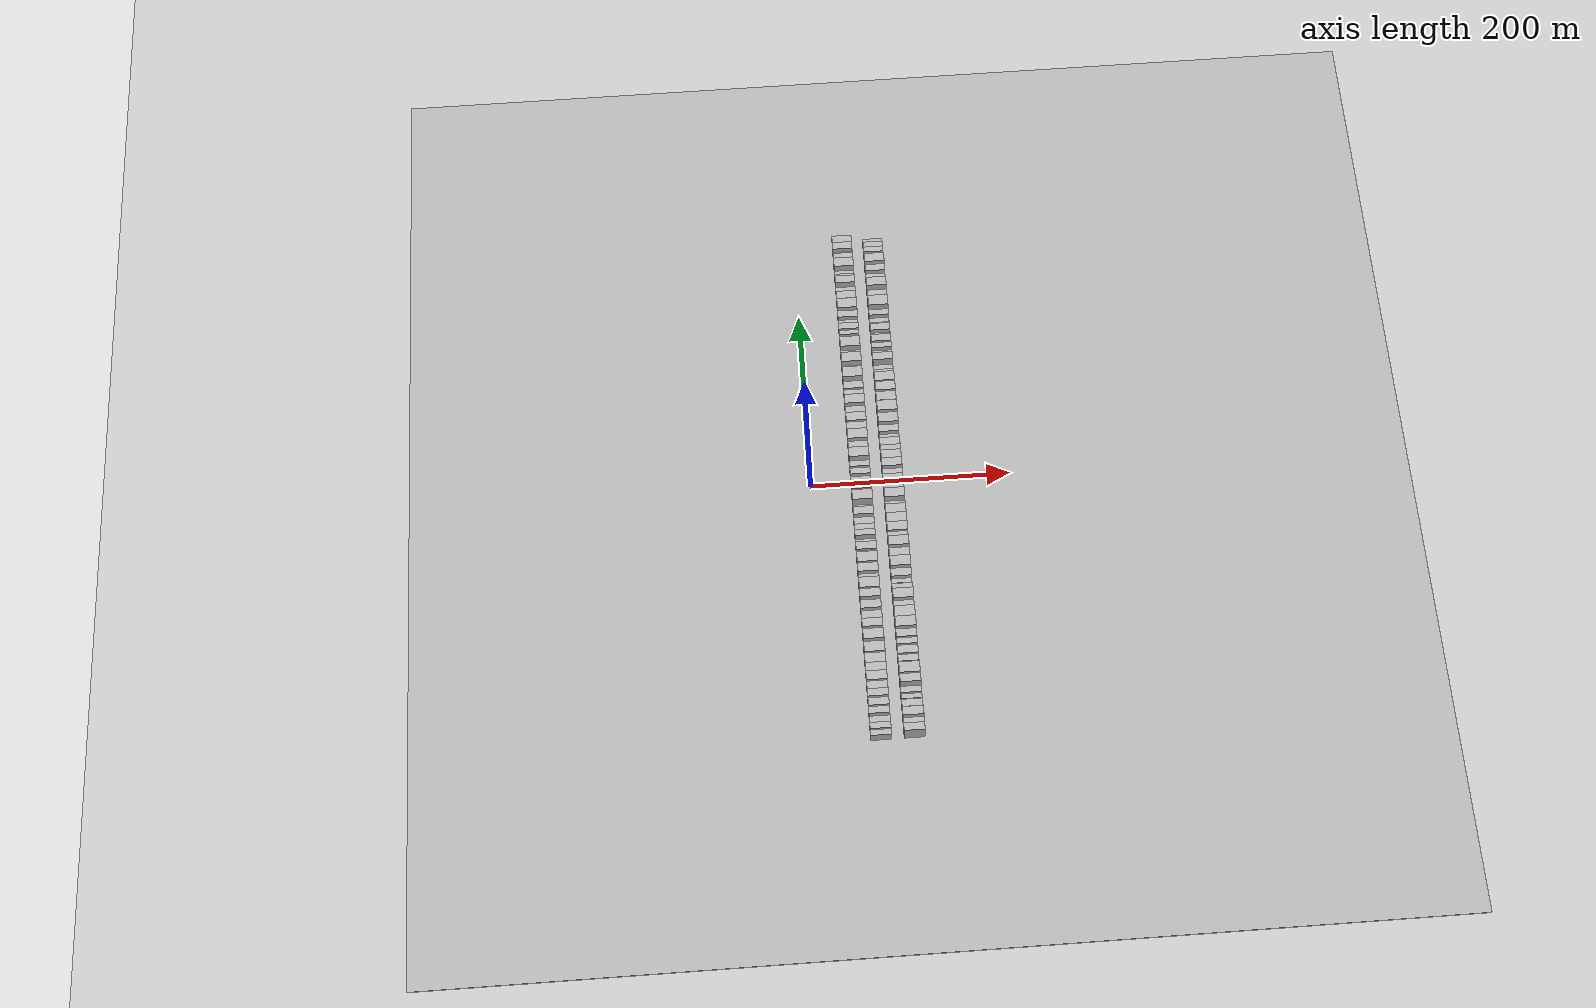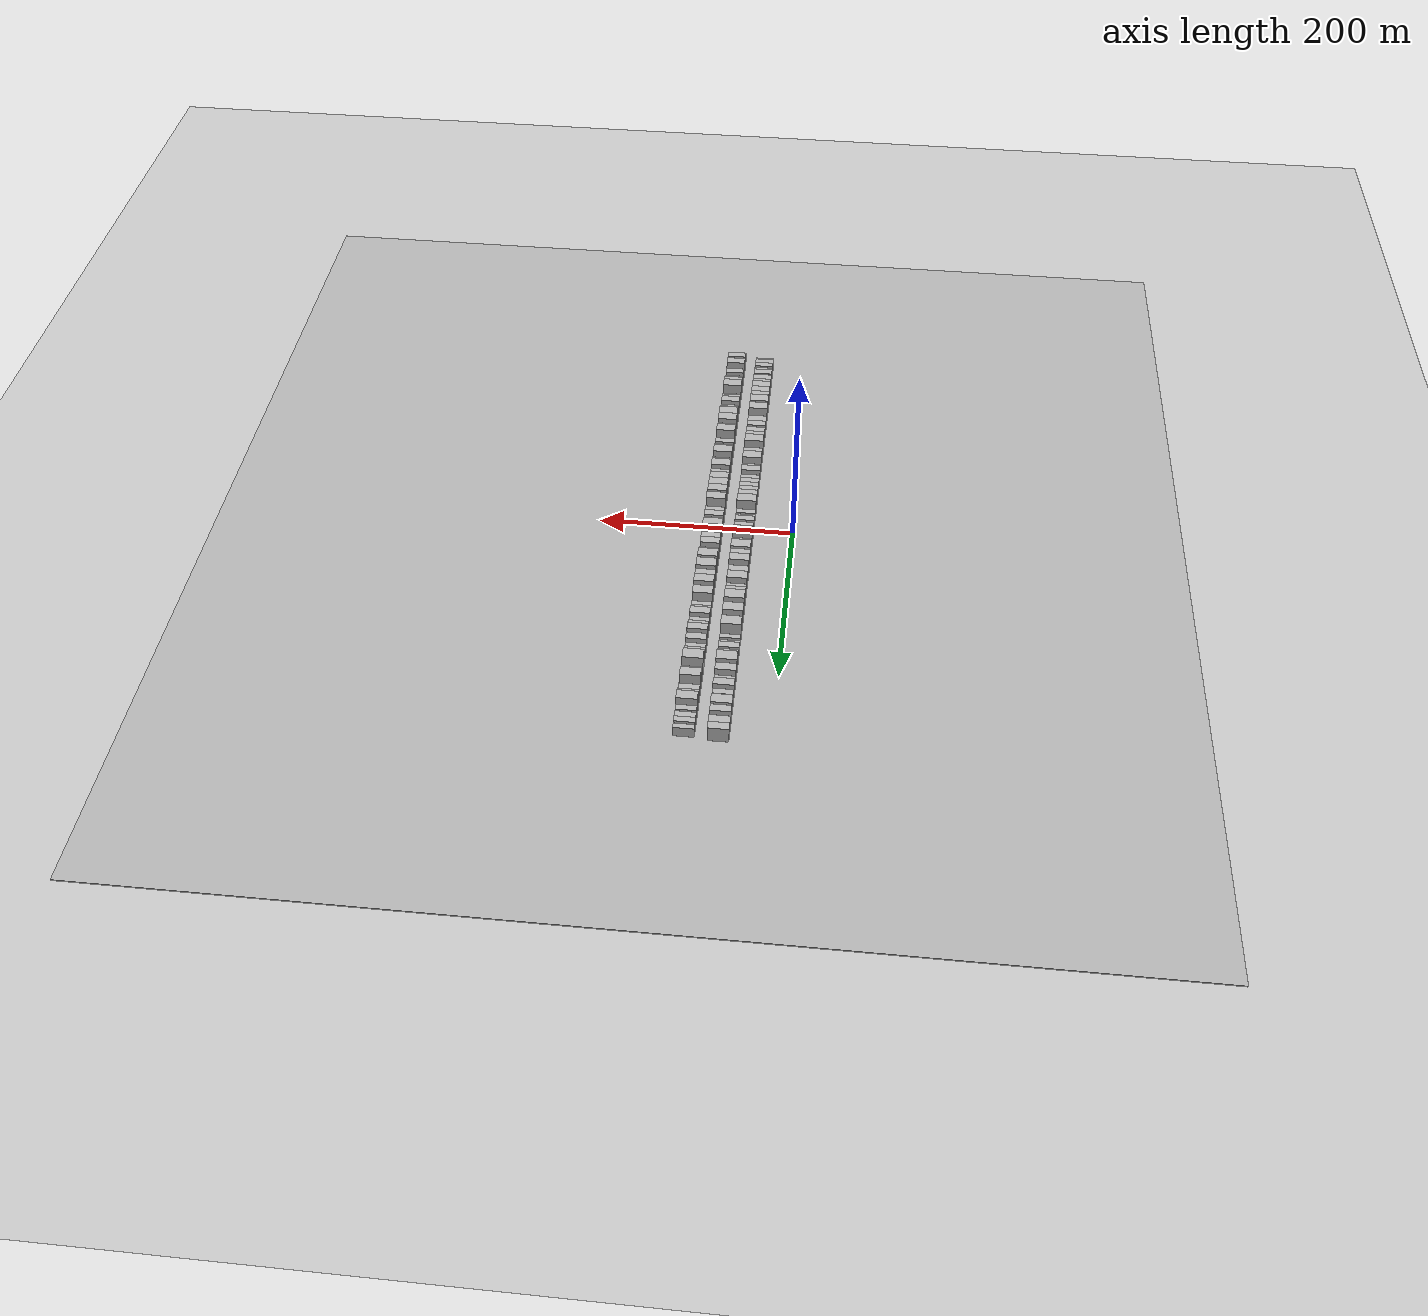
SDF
<?xml version="1.0" encoding="utf-8"?>

<sdf version="1.6">

   <world name="default">

      <gui fullscreen="0">

         <camera name="user_camera">

            <pose>-15 0 4.57585 0 0 0</pose>

            <view_controller>orbit</view_controller>

         </camera>

      </gui>

      <scene>

         <sky>

           <clouds>

             <speed>12</speed>

           </clouds>

         </sky>

         <ambient>0.4 0.4 0.4 1</ambient>

         <background>0.7 0.7 0.7 1</background>

         <shadows>1</shadows>

      </scene>

      <gravity>0 0 -9.8066</gravity>

      <magnetic_field>6e-06 2.3e-05 -4.2e-05</magnetic_field>

      <physics default="0" name="default_physics" type="ode">

         <ode>

            <solver>

               <type>quick</type>

               <iters>10</iters>

               <sor>1.0</sor>

               <use_dynamic_moi_rescaling>0</use_dynamic_moi_rescaling>

            </solver>

            <constraints>

               <cfm>0</cfm>

               <erp>0.2</erp>

               <contact_max_correcting_vel>100</contact_max_correcting_vel>

               <contact_surface_layer>0.001</contact_surface_layer>

            </constraints>

         </ode>

         <max_step_size>0.004</max_step_size>

         <real_time_factor>1</real_time_factor>

         <real_time_update_rate>250</real_time_update_rate>

      </physics>

      <light name="sun" type="directional">

         <cast_shadows>1</cast_shadows>

         <pose>0 0 10 0 0 0</pose>

         <diffuse>0.8 0.8 0.8 1</diffuse>

         <specular>0.2 0.2 0.2 1</specular>

         <attenuation>

            <range>1000</range>

            <constant>0.9</constant>

            <linear>0.01</linear>

            <quadratic>0.001</quadratic>

         </attenuation>

         <direction>-0.5 0.1 -0.9</direction>

      </light>

      <include>

         <name>ground_plane_1</name>

         <uri>model://HANNAS_ground_plane</uri>

         <pose>0 0 0  0 0 0</pose>

      </include>

      <include>

         <name>ground_plane_2</name>

         <uri>model://HANNAS_ground_plane</uri>

         <pose>100 0 0  0 0 0</pose>

      </include>

      <model name="building_1">

         <static>1</static>

         <pose frame="">50.0000 -279.1271 0 0.000000 0.000000 0.000000</pose>

         <link name="link">

            <pose frame="">0 0 6.00 0 0 0</pose>

            <collision name="collision">

               <geometry>

                  <box>

                     <size>20.0000 5.7459 12.0000</size>

                  </box>

               </geometry>

               <max_contacts>10</max_contacts>

               <surface>

                  <contact>

                     <ode/>

                  </contact>

                  <bounce/>

                  <friction>

                     <torsional>

                        <ode/>

                     </torsional>

                     <ode/>

                  </friction>

               </surface>

            </collision>

            <visual name="visual">

               <cast_shadows>0</cast_shadows>

               <geometry>

                  <box>

                     <size>20.0000 5.7459 12.0000</size>

                  </box>

               </geometry>

               <material>

                  <script>

                     <uri>model://HANNAS_wall/materials/scripts</uri>

                     <uri>model://HANNAS_wall/materials/textures</uri>

                     <name>vrc/HANNAS_wall</name>

                  </script>

               </material>

            </visual>

            <self_collide>0</self_collide>

            <enable_wind>0</enable_wind>

            <kinematic>0</kinematic>

         </link>

      </model>

      <model name="building_2">

         <static>1</static>

         <pose frame="">50.0000 -273.0447 0 0.000000 0.000000 0.000000</pose>

         <link name="link">

            <pose frame="">0 0 7.50 0 0 0</pose>

            <collision name="collision">

               <geometry>

                  <box>

                     <size>20.0000 6.4189 15.0000</size>

                  </box>

               </geometry>

               <max_contacts>10</max_contacts>

               <surface>

                  <contact>

                     <ode/>

                  </contact>

                  <bounce/>

                  <friction>

                     <torsional>

                        <ode/>

                     </torsional>

                     <ode/>

                  </friction>

               </surface>

            </collision>

            <visual name="visual">

               <cast_shadows>0</cast_shadows>

               <geometry>

                  <box>

                     <size>20.0000 6.4189 15.0000</size>

                  </box>

               </geometry>

               <material>

                  <script>

                     <uri>model://HANNAS_wall/materials/scripts</uri>

                     <uri>model://HANNAS_wall/materials/textures</uri>

                     <name>vrc/HANNAS_wall</name>

                  </script>

               </material>

            </visual>

            <self_collide>0</self_collide>

            <enable_wind>0</enable_wind>

            <kinematic>0</kinematic>

         </link>

      </model>

      <model name="building_3">

         <static>1</static>

         <pose frame="">50.0000 -266.5574 0 0.000000 0.000000 0.000000</pose>

         <link name="link">

            <pose frame="">0 0 7.50 0 0 0</pose>

            <collision name="collision">

               <geometry>

                  <box>

                     <size>20.0000 6.5558 15.0000</size>

                  </box>

               </geometry>

               <max_contacts>10</max_contacts>

               <surface>

                  <contact>

                     <ode/>

                  </contact>

                  <bounce/>

                  <friction>

                     <torsional>

                        <ode/>

                     </torsional>

                     <ode/>

                  </friction>

               </surface>

            </collision>

            <visual name="visual">

               <cast_shadows>0</cast_shadows>

               <geometry>

                  <box>

                     <size>20.0000 6.5558 15.0000</size>

                  </box>

               </geometry>

               <material>

                  <script>

                     <uri>model://HANNAS_wall/materials/scripts</uri>

                     <uri>model://HANNAS_wall/materials/textures</uri>

                     <name>vrc/HANNAS_wall</name>

                  </script>

               </material>

            </visual>

            <self_collide>0</self_collide>

            <enable_wind>0</enable_wind>

            <kinematic>0</kinematic>

         </link>

      </model>

      <model name="building_4">

         <static>1</static>

         <pose frame="">50.0000 -256.7154 0 0.000000 0.000000 0.000000</pose>

         <link name="link">

            <pose frame="">0 0 7.50 0 0 0</pose>

            <collision name="collision">

               <geometry>

                  <box>

                     <size>20.0000 7.1282 15.0000</size>

                  </box>

               </geometry>

               <max_contacts>10</max_contacts>

               <surface>

                  <contact>

                     <ode/>

                  </contact>

                  <bounce/>

                  <friction>

                     <torsional>

                        <ode/>

                     </torsional>

                     <ode/>

                  </friction>

               </surface>

            </collision>

            <visual name="visual">

               <cast_shadows>0</cast_shadows>

               <geometry>

                  <box>

                     <size>20.0000 7.1282 15.0000</size>

                  </box>

               </geometry>

               <material>

                  <script>

                     <uri>model://HANNAS_wall/materials/scripts</uri>

                     <uri>model://HANNAS_wall/materials/textures</uri>

                     <name>vrc/HANNAS_wall</name>

                  </script>

               </material>

            </visual>

            <self_collide>0</self_collide>

            <enable_wind>0</enable_wind>

            <kinematic>0</kinematic>

         </link>

      </model>

      <model name="building_5">

         <static>1</static>

         <pose frame="">50.0000 -249.2632 0 0.000000 0.000000 0.000000</pose>

         <link name="link">

            <pose frame="">0 0 9.00 0 0 0</pose>

            <collision name="collision">

               <geometry>

                  <box>

                     <size>20.0000 7.7762 18.0000</size>

                  </box>

               </geometry>

               <max_contacts>10</max_contacts>

               <surface>

                  <contact>

                     <ode/>

                  </contact>

                  <bounce/>

                  <friction>

                     <torsional>

                        <ode/>

                     </torsional>

                     <ode/>

                  </friction>

               </surface>

            </collision>

            <visual name="visual">

               <cast_shadows>0</cast_shadows>

               <geometry>

                  <box>

                     <size>20.0000 7.7762 18.0000</size>

                  </box>

               </geometry>

               <material>

                  <script>

                     <uri>model://HANNAS_wall/materials/scripts</uri>

                     <uri>model://HANNAS_wall/materials/textures</uri>

                     <name>vrc/HANNAS_wall</name>

                  </script>

               </material>

            </visual>

            <self_collide>0</self_collide>

            <enable_wind>0</enable_wind>

            <kinematic>0</kinematic>

         </link>

      </model>

      <model name="building_6">

         <static>1</static>

         <pose frame="">50.0000 -239.5126 0 0.000000 0.000000 0.000000</pose>

         <link name="link">

            <pose frame="">0 0 9.00 0 0 0</pose>

            <collision name="collision">

               <geometry>

                  <box>

                     <size>20.0000 7.7250 18.0000</size>

                  </box>

               </geometry>

               <max_contacts>10</max_contacts>

               <surface>

                  <contact>

                     <ode/>

                  </contact>

                  <bounce/>

                  <friction>

                     <torsional>

                        <ode/>

                     </torsional>

                     <ode/>

                  </friction>

               </surface>

            </collision>

            <visual name="visual">

               <cast_shadows>0</cast_shadows>

               <geometry>

                  <box>

                     <size>20.0000 7.7250 18.0000</size>

                  </box>

               </geometry>

               <material>

                  <script>

                     <uri>model://HANNAS_wall/materials/scripts</uri>

                     <uri>model://HANNAS_wall/materials/textures</uri>

                     <name>vrc/HANNAS_wall</name>

                  </script>

               </material>

            </visual>

            <self_collide>0</self_collide>

            <enable_wind>0</enable_wind>

            <kinematic>0</kinematic>

         </link>

      </model>

      <model name="building_7">

         <static>1</static>

         <pose frame="">50.0000 -231.6655 0 0.000000 0.000000 0.000000</pose>

         <link name="link">

            <pose frame="">0 0 9.00 0 0 0</pose>

            <collision name="collision">

               <geometry>

                  <box>

                     <size>20.0000 7.9691 18.0000</size>

                  </box>

               </geometry>

               <max_contacts>10</max_contacts>

               <surface>

                  <contact>

                     <ode/>

                  </contact>

                  <bounce/>

                  <friction>

                     <torsional>

                        <ode/>

                     </torsional>

                     <ode/>

                  </friction>

               </surface>

            </collision>

            <visual name="visual">

               <cast_shadows>0</cast_shadows>

               <geometry>

                  <box>

                     <size>20.0000 7.9691 18.0000</size>

                  </box>

               </geometry>

               <material>

                  <script>

                     <uri>model://HANNAS_wall/materials/scripts</uri>

                     <uri>model://HANNAS_wall/materials/textures</uri>

                     <name>vrc/HANNAS_wall</name>

                  </script>

               </material>

            </visual>

            <self_collide>0</self_collide>

            <enable_wind>0</enable_wind>

            <kinematic>0</kinematic>

         </link>

      </model>

      <model name="building_8">

         <static>1</static>

         <pose frame="">50.0000 -222.8988 0 0.000000 0.000000 0.000000</pose>

         <link name="link">

            <pose frame="">0 0 10.50 0 0 0</pose>

            <collision name="collision">

               <geometry>

                  <box>

                     <size>20.0000 9.5644 21.0000</size>

                  </box>

               </geometry>

               <max_contacts>10</max_contacts>

               <surface>

                  <contact>

                     <ode/>

                  </contact>

                  <bounce/>

                  <friction>

                     <torsional>

                        <ode/>

                     </torsional>

                     <ode/>

                  </friction>

               </surface>

            </collision>

            <visual name="visual">

               <cast_shadows>0</cast_shadows>

               <geometry>

                  <box>

                     <size>20.0000 9.5644 21.0000</size>

                  </box>

               </geometry>

               <material>

                  <script>

                     <uri>model://HANNAS_wall/materials/scripts</uri>

                     <uri>model://HANNAS_wall/materials/textures</uri>

                     <name>vrc/HANNAS_wall</name>

                  </script>

               </material>

            </visual>

            <self_collide>0</self_collide>

            <enable_wind>0</enable_wind>

            <kinematic>0</kinematic>

         </link>

      </model>

      <model name="building_9">

         <static>1</static>

         <pose frame="">50.0000 -213.6746 0 0.000000 0.000000 0.000000</pose>

         <link name="link">

            <pose frame="">0 0 10.50 0 0 0</pose>

            <collision name="collision">

               <geometry>

                  <box>

                     <size>20.0000 8.8841 21.0000</size>

                  </box>

               </geometry>

               <max_contacts>10</max_contacts>

               <surface>

                  <contact>

                     <ode/>

                  </contact>

                  <bounce/>

                  <friction>

                     <torsional>

                        <ode/>

                     </torsional>

                     <ode/>

                  </friction>

               </surface>

            </collision>

            <visual name="visual">

               <cast_shadows>0</cast_shadows>

               <geometry>

                  <box>

                     <size>20.0000 8.8841 21.0000</size>

                  </box>

               </geometry>

               <material>

                  <script>

                     <uri>model://HANNAS_wall/materials/scripts</uri>

                     <uri>model://HANNAS_wall/materials/textures</uri>

                     <name>vrc/HANNAS_wall</name>

                  </script>

               </material>

            </visual>

            <self_collide>0</self_collide>

            <enable_wind>0</enable_wind>

            <kinematic>0</kinematic>

         </link>

      </model>

      <model name="building_10">

         <static>1</static>

         <pose frame="">50.0000 -204.1396 0 0.000000 0.000000 0.000000</pose>

         <link name="link">

            <pose frame="">0 0 10.50 0 0 0</pose>

            <collision name="collision">

               <geometry>

                  <box>

                     <size>20.0000 10.1860 21.0000</size>

                  </box>

               </geometry>

               <max_contacts>10</max_contacts>

               <surface>

                  <contact>

                     <ode/>

                  </contact>

                  <bounce/>

                  <friction>

                     <torsional>

                        <ode/>

                     </torsional>

                     <ode/>

                  </friction>

               </surface>

            </collision>

            <visual name="visual">

               <cast_shadows>0</cast_shadows>

               <geometry>

                  <box>

                     <size>20.0000 10.1860 21.0000</size>

                  </box>

               </geometry>

               <material>

                  <script>

                     <uri>model://HANNAS_wall/materials/scripts</uri>

                     <uri>model://HANNAS_wall/materials/textures</uri>

                     <name>vrc/HANNAS_wall</name>

                  </script>

               </material>

            </visual>

            <self_collide>0</self_collide>

            <enable_wind>0</enable_wind>

            <kinematic>0</kinematic>

         </link>

      </model>

      <model name="building_11">

         <static>1</static>

         <pose frame="">50.0000 -193.5970 0 0.000000 0.000000 0.000000</pose>

         <link name="link">

            <pose frame="">0 0 12.00 0 0 0</pose>

            <collision name="collision">

               <geometry>

                  <box>

                     <size>20.0000 10.8992 24.0000</size>

                  </box>

               </geometry>

               <max_contacts>10</max_contacts>

               <surface>

                  <contact>

                     <ode/>

                  </contact>

                  <bounce/>

                  <friction>

                     <torsional>

                        <ode/>

                     </torsional>

                     <ode/>

                  </friction>

               </surface>

            </collision>

            <visual name="visual">

               <cast_shadows>0</cast_shadows>

               <geometry>

                  <box>

                     <size>20.0000 10.8992 24.0000</size>

                  </box>

               </geometry>

               <material>

                  <script>

                     <uri>model://HANNAS_wall/materials/scripts</uri>

                     <uri>model://HANNAS_wall/materials/textures</uri>

                     <name>vrc/HANNAS_wall</name>

                  </script>

               </material>

            </visual>

            <self_collide>0</self_collide>

            <enable_wind>0</enable_wind>

            <kinematic>0</kinematic>

         </link>

      </model>

      <model name="building_12">

         <static>1</static>

         <pose frame="">50.0000 -179.7389 0 0.000000 0.000000 0.000000</pose>

         <link name="link">

            <pose frame="">0 0 12.00 0 0 0</pose>

            <collision name="collision">

               <geometry>

                  <box>

                     <size>20.0000 10.8170 24.0000</size>

                  </box>

               </geometry>

               <max_contacts>10</max_contacts>

               <surface>

                  <contact>

                     <ode/>

                  </contact>

                  <bounce/>

                  <friction>

                     <torsional>

                        <ode/>

                     </torsional>

                     <ode/>

                  </friction>

               </surface>

            </collision>

            <visual name="visual">

               <cast_shadows>0</cast_shadows>

               <geometry>

                  <box>

                     <size>20.0000 10.8170 24.0000</size>

                  </box>

               </geometry>

               <material>

                  <script>

                     <uri>model://HANNAS_wall/materials/scripts</uri>

                     <uri>model://HANNAS_wall/materials/textures</uri>

                     <name>vrc/HANNAS_wall</name>

                  </script>

               </material>

            </visual>

            <self_collide>0</self_collide>

            <enable_wind>0</enable_wind>

            <kinematic>0</kinematic>

         </link>

      </model>

      <model name="building_13">

         <static>1</static>

         <pose frame="">50.0000 -171.6334 0 0.000000 0.000000 0.000000</pose>

         <link name="link">

            <pose frame="">0 0 6.00 0 0 0</pose>

            <collision name="collision">

               <geometry>

                  <box>

                     <size>20.0000 5.3941 12.0000</size>

                  </box>

               </geometry>

               <max_contacts>10</max_contacts>

               <surface>

                  <contact>

                     <ode/>

                  </contact>

                  <bounce/>

                  <friction>

                     <torsional>

                        <ode/>

                     </torsional>

                     <ode/>

                  </friction>

               </surface>

            </collision>

            <visual name="visual">

               <cast_shadows>0</cast_shadows>

               <geometry>

                  <box>

                     <size>20.0000 5.3941 12.0000</size>

                  </box>

               </geometry>

               <material>

                  <script>

                     <uri>model://HANNAS_wall/materials/scripts</uri>

                     <uri>model://HANNAS_wall/materials/textures</uri>

                     <name>vrc/HANNAS_wall</name>

                  </script>

               </material>

            </visual>

            <self_collide>0</self_collide>

            <enable_wind>0</enable_wind>

            <kinematic>0</kinematic>

         </link>

      </model>

      <model name="building_14">

         <static>1</static>

         <pose frame="">50.0000 -164.4834 0 0.000000 0.000000 0.000000</pose>

         <link name="link">

            <pose frame="">0 0 9.00 0 0 0</pose>

            <collision name="collision">

               <geometry>

                  <box>

                     <size>20.0000 8.9060 18.0000</size>

                  </box>

               </geometry>

               <max_contacts>10</max_contacts>

               <surface>

                  <contact>

                     <ode/>

                  </contact>

                  <bounce/>

                  <friction>

                     <torsional>

                        <ode/>

                     </torsional>

                     <ode/>

                  </friction>

               </surface>

            </collision>

            <visual name="visual">

               <cast_shadows>0</cast_shadows>

               <geometry>

                  <box>

                     <size>20.0000 8.9060 18.0000</size>

                  </box>

               </geometry>

               <material>

                  <script>

                     <uri>model://HANNAS_wall/materials/scripts</uri>

                     <uri>model://HANNAS_wall/materials/textures</uri>

                     <name>vrc/HANNAS_wall</name>

                  </script>

               </material>

            </visual>

            <self_collide>0</self_collide>

            <enable_wind>0</enable_wind>

            <kinematic>0</kinematic>

         </link>

      </model>

      <model name="building_15">

         <static>1</static>

         <pose frame="">50.0000 -155.9993 0 0.000000 0.000000 0.000000</pose>

         <link name="link">

            <pose frame="">0 0 9.00 0 0 0</pose>

            <collision name="collision">

               <geometry>

                  <box>

                     <size>20.0000 8.0620 18.0000</size>

                  </box>

               </geometry>

               <max_contacts>10</max_contacts>

               <surface>

                  <contact>

                     <ode/>

                  </contact>

                  <bounce/>

                  <friction>

                     <torsional>

                        <ode/>

                     </torsional>

                     <ode/>

                  </friction>

               </surface>

            </collision>

            <visual name="visual">

               <cast_shadows>0</cast_shadows>

               <geometry>

                  <box>

                     <size>20.0000 8.0620 18.0000</size>

                  </box>

               </geometry>

               <material>

                  <script>

                     <uri>model://HANNAS_wall/materials/scripts</uri>

                     <uri>model://HANNAS_wall/materials/textures</uri>

                     <name>vrc/HANNAS_wall</name>

                  </script>

               </material>

            </visual>

            <self_collide>0</self_collide>

            <enable_wind>0</enable_wind>

            <kinematic>0</kinematic>

         </link>

      </model>

      <model name="building_16">

         <static>1</static>

         <pose frame="">50.0000 -144.5254 0 0.000000 0.000000 0.000000</pose>

         <link name="link">

            <pose frame="">0 0 9.00 0 0 0</pose>

            <collision name="collision">

               <geometry>

                  <box>

                     <size>20.0000 8.8857 18.0000</size>

                  </box>

               </geometry>

               <max_contacts>10</max_contacts>

               <surface>

                  <contact>

                     <ode/>

                  </contact>

                  <bounce/>

                  <friction>

                     <torsional>

                        <ode/>

                     </torsional>

                     <ode/>

                  </friction>

               </surface>

            </collision>

            <visual name="visual">

               <cast_shadows>0</cast_shadows>

               <geometry>

                  <box>

                     <size>20.0000 8.8857 18.0000</size>

                  </box>

               </geometry>

               <material>

                  <script>

                     <uri>model://HANNAS_wall/materials/scripts</uri>

                     <uri>model://HANNAS_wall/materials/textures</uri>

                     <name>vrc/HANNAS_wall</name>

                  </script>

               </material>

            </visual>

            <self_collide>0</self_collide>

            <enable_wind>0</enable_wind>

            <kinematic>0</kinematic>

         </link>

      </model>

      <model name="building_17">

         <static>1</static>

         <pose frame="">50.0000 -133.6724 0 0.000000 0.000000 0.000000</pose>

         <link name="link">

            <pose frame="">0 0 10.50 0 0 0</pose>

            <collision name="collision">

               <geometry>

                  <box>

                     <size>20.0000 8.8204 21.0000</size>

                  </box>

               </geometry>

               <max_contacts>10</max_contacts>

               <surface>

                  <contact>

                     <ode/>

                  </contact>

                  <bounce/>

                  <friction>

                     <torsional>

                        <ode/>

                     </torsional>

                     <ode/>

                  </friction>

               </surface>

            </collision>

            <visual name="visual">

               <cast_shadows>0</cast_shadows>

               <geometry>

                  <box>

                     <size>20.0000 8.8204 21.0000</size>

                  </box>

               </geometry>

               <material>

                  <script>

                     <uri>model://HANNAS_wall/materials/scripts</uri>

                     <uri>model://HANNAS_wall/materials/textures</uri>

                     <name>vrc/HANNAS_wall</name>

                  </script>

               </material>

            </visual>

            <self_collide>0</self_collide>

            <enable_wind>0</enable_wind>

            <kinematic>0</kinematic>

         </link>

      </model>

      <model name="building_18">

         <static>1</static>

         <pose frame="">50.0000 -123.7028 0 0.000000 0.000000 0.000000</pose>

         <link name="link">

            <pose frame="">0 0 12.00 0 0 0</pose>

            <collision name="collision">

               <geometry>

                  <box>

                     <size>20.0000 11.1187 24.0000</size>

                  </box>

               </geometry>

               <max_contacts>10</max_contacts>

               <surface>

                  <contact>

                     <ode/>

                  </contact>

                  <bounce/>

                  <friction>

                     <torsional>

                        <ode/>

                     </torsional>

                     <ode/>

                  </friction>

               </surface>

            </collision>

            <visual name="visual">

               <cast_shadows>0</cast_shadows>

               <geometry>

                  <box>

                     <size>20.0000 11.1187 24.0000</size>

                  </box>

               </geometry>

               <material>

                  <script>

                     <uri>model://HANNAS_wall/materials/scripts</uri>

                     <uri>model://HANNAS_wall/materials/textures</uri>

                     <name>vrc/HANNAS_wall</name>

                  </script>

               </material>

            </visual>

            <self_collide>0</self_collide>

            <enable_wind>0</enable_wind>

            <kinematic>0</kinematic>

         </link>

      </model>

      <model name="building_19">

         <static>1</static>

         <pose frame="">50.0000 -113.0769 0 0.000000 0.000000 0.000000</pose>

         <link name="link">

            <pose frame="">0 0 7.50 0 0 0</pose>

            <collision name="collision">

               <geometry>

                  <box>

                     <size>20.0000 6.1330 15.0000</size>

                  </box>

               </geometry>

               <max_contacts>10</max_contacts>

               <surface>

                  <contact>

                     <ode/>

                  </contact>

                  <bounce/>

                  <friction>

                     <torsional>

                        <ode/>

                     </torsional>

                     <ode/>

                  </friction>

               </surface>

            </collision>

            <visual name="visual">

               <cast_shadows>0</cast_shadows>

               <geometry>

                  <box>

                     <size>20.0000 6.1330 15.0000</size>

                  </box>

               </geometry>

               <material>

                  <script>

                     <uri>model://HANNAS_wall/materials/scripts</uri>

                     <uri>model://HANNAS_wall/materials/textures</uri>

                     <name>vrc/HANNAS_wall</name>

                  </script>

               </material>

            </visual>

            <self_collide>0</self_collide>

            <enable_wind>0</enable_wind>

            <kinematic>0</kinematic>

         </link>

      </model>

      <model name="building_20">

         <static>1</static>

         <pose frame="">50.0000 -105.4436 0 0.000000 0.000000 0.000000</pose>

         <link name="link">

            <pose frame="">0 0 10.50 0 0 0</pose>

            <collision name="collision">

               <geometry>

                  <box>

                     <size>20.0000 9.1338 21.0000</size>

                  </box>

               </geometry>

               <max_contacts>10</max_contacts>

               <surface>

                  <contact>

                     <ode/>

                  </contact>

                  <bounce/>

                  <friction>

                     <torsional>

                        <ode/>

                     </torsional>

                     <ode/>

                  </friction>

               </surface>

            </collision>

            <visual name="visual">

               <cast_shadows>0</cast_shadows>

               <geometry>

                  <box>

                     <size>20.0000 9.1338 21.0000</size>

                  </box>

               </geometry>

               <material>

                  <script>

                     <uri>model://HANNAS_wall/materials/scripts</uri>

                     <uri>model://HANNAS_wall/materials/textures</uri>

                     <name>vrc/HANNAS_wall</name>

                  </script>

               </material>

            </visual>

            <self_collide>0</self_collide>

            <enable_wind>0</enable_wind>

            <kinematic>0</kinematic>

         </link>

      </model>

      <model name="building_21">

         <static>1</static>

         <pose frame="">50.0000 -95.4409 0 0.000000 0.000000 0.000000</pose>

         <link name="link">

            <pose frame="">0 0 12.00 0 0 0</pose>

            <collision name="collision">

               <geometry>

                  <box>

                     <size>20.0000 10.8715 24.0000</size>

                  </box>

               </geometry>

               <max_contacts>10</max_contacts>

               <surface>

                  <contact>

                     <ode/>

                  </contact>

                  <bounce/>

                  <friction>

                     <torsional>

                        <ode/>

                     </torsional>

                     <ode/>

                  </friction>

               </surface>

            </collision>

            <visual name="visual">

               <cast_shadows>0</cast_shadows>

               <geometry>

                  <box>

                     <size>20.0000 10.8715 24.0000</size>

                  </box>

               </geometry>

               <material>

                  <script>

                     <uri>model://HANNAS_wall/materials/scripts</uri>

                     <uri>model://HANNAS_wall/materials/textures</uri>

                     <name>vrc/HANNAS_wall</name>

                  </script>

               </material>

            </visual>

            <self_collide>0</self_collide>

            <enable_wind>0</enable_wind>

            <kinematic>0</kinematic>

         </link>

      </model>

      <model name="building_22">

         <static>1</static>

         <pose frame="">50.0000 -86.9923 0 0.000000 0.000000 0.000000</pose>

         <link name="link">

            <pose frame="">0 0 7.50 0 0 0</pose>

            <collision name="collision">

               <geometry>

                  <box>

                     <size>20.0000 6.0256 15.0000</size>

                  </box>

               </geometry>

               <max_contacts>10</max_contacts>

               <surface>

                  <contact>

                     <ode/>

                  </contact>

                  <bounce/>

                  <friction>

                     <torsional>

                        <ode/>

                     </torsional>

                     <ode/>

                  </friction>

               </surface>

            </collision>

            <visual name="visual">

               <cast_shadows>0</cast_shadows>

               <geometry>

                  <box>

                     <size>20.0000 6.0256 15.0000</size>

                  </box>

               </geometry>

               <material>

                  <script>

                     <uri>model://HANNAS_wall/materials/scripts</uri>

                     <uri>model://HANNAS_wall/materials/textures</uri>

                     <name>vrc/HANNAS_wall</name>

                  </script>

               </material>

            </visual>

            <self_collide>0</self_collide>

            <enable_wind>0</enable_wind>

            <kinematic>0</kinematic>

         </link>

      </model>

      <model name="building_23">

         <static>1</static>

         <pose frame="">50.0000 -79.8421 0 0.000000 0.000000 0.000000</pose>

         <link name="link">

            <pose frame="">0 0 9.00 0 0 0</pose>

            <collision name="collision">

               <geometry>

                  <box>

                     <size>20.0000 8.2749 18.0000</size>

                  </box>

               </geometry>

               <max_contacts>10</max_contacts>

               <surface>

                  <contact>

                     <ode/>

                  </contact>

                  <bounce/>

                  <friction>

                     <torsional>

                        <ode/>

                     </torsional>

                     <ode/>

                  </friction>

               </surface>

            </collision>

            <visual name="visual">

               <cast_shadows>0</cast_shadows>

               <geometry>

                  <box>

                     <size>20.0000 8.2749 18.0000</size>

                  </box>

               </geometry>

               <material>

                  <script>

                     <uri>model://HANNAS_wall/materials/scripts</uri>

                     <uri>model://HANNAS_wall/materials/textures</uri>

                     <name>vrc/HANNAS_wall</name>

                  </script>

               </material>

            </visual>

            <self_collide>0</self_collide>

            <enable_wind>0</enable_wind>

            <kinematic>0</kinematic>

         </link>

      </model>

      <model name="building_24">

         <static>1</static>

         <pose frame="">50.0000 -72.7355 0 0.000000 0.000000 0.000000</pose>

         <link name="link">

            <pose frame="">0 0 6.00 0 0 0</pose>

            <collision name="collision">

               <geometry>

                  <box>

                     <size>20.0000 5.9383 12.0000</size>

                  </box>

               </geometry>

               <max_contacts>10</max_contacts>

               <surface>

                  <contact>

                     <ode/>

                  </contact>

                  <bounce/>

                  <friction>

                     <torsional>

                        <ode/>

                     </torsional>

                     <ode/>

                  </friction>

               </surface>

            </collision>

            <visual name="visual">

               <cast_shadows>0</cast_shadows>

               <geometry>

                  <box>

                     <size>20.0000 5.9383 12.0000</size>

                  </box>

               </geometry>

               <material>

                  <script>

                     <uri>model://HANNAS_wall/materials/scripts</uri>

                     <uri>model://HANNAS_wall/materials/textures</uri>

                     <name>vrc/HANNAS_wall</name>

                  </script>

               </material>

            </visual>

            <self_collide>0</self_collide>

            <enable_wind>0</enable_wind>

            <kinematic>0</kinematic>

         </link>

      </model>

      <model name="building_25">

         <static>1</static>

         <pose frame="">50.0000 -63.4808 0 0.000000 0.000000 0.000000</pose>

         <link name="link">

            <pose frame="">0 0 7.50 0 0 0</pose>

            <collision name="collision">

               <geometry>

                  <box>

                     <size>20.0000 6.5712 15.0000</size>

                  </box>

               </geometry>

               <max_contacts>10</max_contacts>

               <surface>

                  <contact>

                     <ode/>

                  </contact>

                  <bounce/>

                  <friction>

                     <torsional>

                        <ode/>

                     </torsional>

                     <ode/>

                  </friction>

               </surface>

            </collision>

            <visual name="visual">

               <cast_shadows>0</cast_shadows>

               <geometry>

                  <box>

                     <size>20.0000 6.5712 15.0000</size>

                  </box>

               </geometry>

               <material>

                  <script>

                     <uri>model://HANNAS_wall/materials/scripts</uri>

                     <uri>model://HANNAS_wall/materials/textures</uri>

                     <name>vrc/HANNAS_wall</name>

                  </script>

               </material>

            </visual>

            <self_collide>0</self_collide>

            <enable_wind>0</enable_wind>

            <kinematic>0</kinematic>

         </link>

      </model>

      <model name="building_26">

         <static>1</static>

         <pose frame="">50.0000 -57.1335 0 0.000000 0.000000 0.000000</pose>

         <link name="link">

            <pose frame="">0 0 7.50 0 0 0</pose>

            <collision name="collision">

               <geometry>

                  <box>

                     <size>20.0000 6.1234 15.0000</size>

                  </box>

               </geometry>

               <max_contacts>10</max_contacts>

               <surface>

                  <contact>

                     <ode/>

                  </contact>

                  <bounce/>

                  <friction>

                     <torsional>

                        <ode/>

                     </torsional>

                     <ode/>

                  </friction>

               </surface>

            </collision>

            <visual name="visual">

               <cast_shadows>0</cast_shadows>

               <geometry>

                  <box>

                     <size>20.0000 6.1234 15.0000</size>

                  </box>

               </geometry>

               <material>

                  <script>

                     <uri>model://HANNAS_wall/materials/scripts</uri>

                     <uri>model://HANNAS_wall/materials/textures</uri>

                     <name>vrc/HANNAS_wall</name>

                  </script>

               </material>

            </visual>

            <self_collide>0</self_collide>

            <enable_wind>0</enable_wind>

            <kinematic>0</kinematic>

         </link>

      </model>

      <model name="building_27">

         <static>1</static>

         <pose frame="">50.0000 -50.3300 0 0.000000 0.000000 0.000000</pose>

         <link name="link">

            <pose frame="">0 0 7.50 0 0 0</pose>

            <collision name="collision">

               <geometry>

                  <box>

                     <size>20.0000 7.4836 15.0000</size>

                  </box>

               </geometry>

               <max_contacts>10</max_contacts>

               <surface>

                  <contact>

                     <ode/>

                  </contact>

                  <bounce/>

                  <friction>

                     <torsional>

                        <ode/>

                     </torsional>

                     <ode/>

                  </friction>

               </surface>

            </collision>

            <visual name="visual">

               <cast_shadows>0</cast_shadows>

               <geometry>

                  <box>

                     <size>20.0000 7.4836 15.0000</size>

                  </box>

               </geometry>

               <material>

                  <script>

                     <uri>model://HANNAS_wall/materials/scripts</uri>

                     <uri>model://HANNAS_wall/materials/textures</uri>

                     <name>vrc/HANNAS_wall</name>

                  </script>

               </material>

            </visual>

            <self_collide>0</self_collide>

            <enable_wind>0</enable_wind>

            <kinematic>0</kinematic>

         </link>

      </model>

      <model name="building_28">

         <static>1</static>

         <pose frame="">50.0000 -40.3226 0 0.000000 0.000000 0.000000</pose>

         <link name="link">

            <pose frame="">0 0 9.00 0 0 0</pose>

            <collision name="collision">

               <geometry>

                  <box>

                     <size>20.0000 8.5311 18.0000</size>

                  </box>

               </geometry>

               <max_contacts>10</max_contacts>

               <surface>

                  <contact>

                     <ode/>

                  </contact>

                  <bounce/>

                  <friction>

                     <torsional>

                        <ode/>

                     </torsional>

                     <ode/>

                  </friction>

               </surface>

            </collision>

            <visual name="visual">

               <cast_shadows>0</cast_shadows>

               <geometry>

                  <box>

                     <size>20.0000 8.5311 18.0000</size>

                  </box>

               </geometry>

               <material>

                  <script>

                     <uri>model://HANNAS_wall/materials/scripts</uri>

                     <uri>model://HANNAS_wall/materials/textures</uri>

                     <name>vrc/HANNAS_wall</name>

                  </script>

               </material>

            </visual>

            <self_collide>0</self_collide>

            <enable_wind>0</enable_wind>

            <kinematic>0</kinematic>

         </link>

      </model>

      <model name="building_29">

         <static>1</static>

         <pose frame="">50.0000 -33.5444 0 0.000000 0.000000 0.000000</pose>

         <link name="link">

            <pose frame="">0 0 6.00 0 0 0</pose>

            <collision name="collision">

               <geometry>

                  <box>

                     <size>20.0000 5.0253 12.0000</size>

                  </box>

               </geometry>

               <max_contacts>10</max_contacts>

               <surface>

                  <contact>

                     <ode/>

                  </contact>

                  <bounce/>

                  <friction>

                     <torsional>

                        <ode/>

                     </torsional>

                     <ode/>

                  </friction>

               </surface>

            </collision>

            <visual name="visual">

               <cast_shadows>0</cast_shadows>

               <geometry>

                  <box>

                     <size>20.0000 5.0253 12.0000</size>

                  </box>

               </geometry>

               <material>

                  <script>

                     <uri>model://HANNAS_wall/materials/scripts</uri>

                     <uri>model://HANNAS_wall/materials/textures</uri>

                     <name>vrc/HANNAS_wall</name>

                  </script>

               </material>

            </visual>

            <self_collide>0</self_collide>

            <enable_wind>0</enable_wind>

            <kinematic>0</kinematic>

         </link>

      </model>

      <model name="building_30">

         <static>1</static>

         <pose frame="">50.0000 -25.5399 0 0.000000 0.000000 0.000000</pose>

         <link name="link">

            <pose frame="">0 0 12.00 0 0 0</pose>

            <collision name="collision">

               <geometry>

                  <box>

                     <size>20.0000 10.9839 24.0000</size>

                  </box>

               </geometry>

               <max_contacts>10</max_contacts>

               <surface>

                  <contact>

                     <ode/>

                  </contact>

                  <bounce/>

                  <friction>

                     <torsional>

                        <ode/>

                     </torsional>

                     <ode/>

                  </friction>

               </surface>

            </collision>

            <visual name="visual">

               <cast_shadows>0</cast_shadows>

               <geometry>

                  <box>

                     <size>20.0000 10.9839 24.0000</size>

                  </box>

               </geometry>

               <material>

                  <script>

                     <uri>model://HANNAS_wall/materials/scripts</uri>

                     <uri>model://HANNAS_wall/materials/textures</uri>

                     <name>vrc/HANNAS_wall</name>

                  </script>

               </material>

            </visual>

            <self_collide>0</self_collide>

            <enable_wind>0</enable_wind>

            <kinematic>0</kinematic>

         </link>

      </model>

      <model name="building_31">

         <static>1</static>

         <pose frame="">50.0000 -17.0664 0 0.000000 0.000000 0.000000</pose>

         <link name="link">

            <pose frame="">0 0 6.00 0 0 0</pose>

            <collision name="collision">

               <geometry>

                  <box>

                     <size>20.0000 5.9630 12.0000</size>

                  </box>

               </geometry>

               <max_contacts>10</max_contacts>

               <surface>

                  <contact>

                     <ode/>

                  </contact>

                  <bounce/>

                  <friction>

                     <torsional>

                        <ode/>

                     </torsional>

                     <ode/>

                  </friction>

               </surface>

            </collision>

            <visual name="visual">

               <cast_shadows>0</cast_shadows>

               <geometry>

                  <box>

                     <size>20.0000 5.9630 12.0000</size>

                  </box>

               </geometry>

               <material>

                  <script>

                     <uri>model://HANNAS_wall/materials/scripts</uri>

                     <uri>model://HANNAS_wall/materials/textures</uri>

                     <name>vrc/HANNAS_wall</name>

                  </script>

               </material>

            </visual>

            <self_collide>0</self_collide>

            <enable_wind>0</enable_wind>

            <kinematic>0</kinematic>

         </link>

      </model>

      <model name="building_32">

         <static>1</static>

         <pose frame="">50.0000 -9.5137 0 0.000000 0.000000 0.000000</pose>

         <link name="link">

            <pose frame="">0 0 6.00 0 0 0</pose>

            <collision name="collision">

               <geometry>

                  <box>

                     <size>20.0000 5.1426 12.0000</size>

                  </box>

               </geometry>

               <max_contacts>10</max_contacts>

               <surface>

                  <contact>

                     <ode/>

                  </contact>

                  <bounce/>

                  <friction>

                     <torsional>

                        <ode/>

                     </torsional>

                     <ode/>

                  </friction>

               </surface>

            </collision>

            <visual name="visual">

               <cast_shadows>0</cast_shadows>

               <geometry>

                  <box>

                     <size>20.0000 5.1426 12.0000</size>

                  </box>

               </geometry>

               <material>

                  <script>

                     <uri>model://HANNAS_wall/materials/scripts</uri>

                     <uri>model://HANNAS_wall/materials/textures</uri>

                     <name>vrc/HANNAS_wall</name>

                  </script>

               </material>

            </visual>

            <self_collide>0</self_collide>

            <enable_wind>0</enable_wind>

            <kinematic>0</kinematic>

         </link>

      </model>

      <model name="building_33">

         <static>1</static>

         <pose frame="">50.0000 -3.4888 0 0.000000 0.000000 0.000000</pose>

         <link name="link">

            <pose frame="">0 0 7.50 0 0 0</pose>

            <collision name="collision">

               <geometry>

                  <box>

                     <size>20.0000 6.9071 15.0000</size>

                  </box>

               </geometry>

               <max_contacts>10</max_contacts>

               <surface>

                  <contact>

                     <ode/>

                  </contact>

                  <bounce/>

                  <friction>

                     <torsional>

                        <ode/>

                     </torsional>

                     <ode/>

                  </friction>

               </surface>

            </collision>

            <visual name="visual">

               <cast_shadows>0</cast_shadows>

               <geometry>

                  <box>

                     <size>20.0000 6.9071 15.0000</size>

                  </box>

               </geometry>

               <material>

                  <script>

                     <uri>model://HANNAS_wall/materials/scripts</uri>

                     <uri>model://HANNAS_wall/materials/textures</uri>

                     <name>vrc/HANNAS_wall</name>

                  </script>

               </material>

            </visual>

            <self_collide>0</self_collide>

            <enable_wind>0</enable_wind>

            <kinematic>0</kinematic>

         </link>

      </model>

      <model name="building_34">

         <static>1</static>

         <pose frame="">50.0000 6.3638 0 0.000000 0.000000 0.000000</pose>

         <link name="link">

            <pose frame="">0 0 7.50 0 0 0</pose>

            <collision name="collision">

               <geometry>

                  <box>

                     <size>20.0000 6.7982 15.0000</size>

                  </box>

               </geometry>

               <max_contacts>10</max_contacts>

               <surface>

                  <contact>

                     <ode/>

                  </contact>

                  <bounce/>

                  <friction>

                     <torsional>

                        <ode/>

                     </torsional>

                     <ode/>

                  </friction>

               </surface>

            </collision>

            <visual name="visual">

               <cast_shadows>0</cast_shadows>

               <geometry>

                  <box>

                     <size>20.0000 6.7982 15.0000</size>

                  </box>

               </geometry>

               <material>

                  <script>

                     <uri>model://HANNAS_wall/materials/scripts</uri>

                     <uri>model://HANNAS_wall/materials/textures</uri>

                     <name>vrc/HANNAS_wall</name>

                  </script>

               </material>

            </visual>

            <self_collide>0</self_collide>

            <enable_wind>0</enable_wind>

            <kinematic>0</kinematic>

         </link>

      </model>

      <model name="building_35">

         <static>1</static>

         <pose frame="">50.0000 14.8870 0 0.000000 0.000000 0.000000</pose>

         <link name="link">

            <pose frame="">0 0 7.50 0 0 0</pose>

            <collision name="collision">

               <geometry>

                  <box>

                     <size>20.0000 6.2482 15.0000</size>

                  </box>

               </geometry>

               <max_contacts>10</max_contacts>

               <surface>

                  <contact>

                     <ode/>

                  </contact>

                  <bounce/>

                  <friction>

                     <torsional>

                        <ode/>

                     </torsional>

                     <ode/>

                  </friction>

               </surface>

            </collision>

            <visual name="visual">

               <cast_shadows>0</cast_shadows>

               <geometry>

                  <box>

                     <size>20.0000 6.2482 15.0000</size>

                  </box>

               </geometry>

               <material>

                  <script>

                     <uri>model://HANNAS_wall/materials/scripts</uri>

                     <uri>model://HANNAS_wall/materials/textures</uri>

                     <name>vrc/HANNAS_wall</name>

                  </script>

               </material>

            </visual>

            <self_collide>0</self_collide>

            <enable_wind>0</enable_wind>

            <kinematic>0</kinematic>

         </link>

      </model>

      <model name="building_36">

         <static>1</static>

         <pose frame="">50.0000 23.4039 0 0.000000 0.000000 0.000000</pose>

         <link name="link">

            <pose frame="">0 0 12.00 0 0 0</pose>

            <collision name="collision">

               <geometry>

                  <box>

                     <size>20.0000 10.7855 24.0000</size>

                  </box>

               </geometry>

               <max_contacts>10</max_contacts>

               <surface>

                  <contact>

                     <ode/>

                  </contact>

                  <bounce/>

                  <friction>

                     <torsional>

                        <ode/>

                     </torsional>

                     <ode/>

                  </friction>

               </surface>

            </collision>

            <visual name="visual">

               <cast_shadows>0</cast_shadows>

               <geometry>

                  <box>

                     <size>20.0000 10.7855 24.0000</size>

                  </box>

               </geometry>

               <material>

                  <script>

                     <uri>model://HANNAS_wall/materials/scripts</uri>

                     <uri>model://HANNAS_wall/materials/textures</uri>

                     <name>vrc/HANNAS_wall</name>

                  </script>

               </material>

            </visual>

            <self_collide>0</self_collide>

            <enable_wind>0</enable_wind>

            <kinematic>0</kinematic>

         </link>

      </model>

      <model name="building_37">

         <static>1</static>

         <pose frame="">50.0000 34.9487 0 0.000000 0.000000 0.000000</pose>

         <link name="link">

            <pose frame="">0 0 9.00 0 0 0</pose>

            <collision name="collision">

               <geometry>

                  <box>

                     <size>20.0000 8.3042 18.0000</size>

                  </box>

               </geometry>

               <max_contacts>10</max_contacts>

               <surface>

                  <contact>

                     <ode/>

                  </contact>

                  <bounce/>

                  <friction>

                     <torsional>

                        <ode/>

                     </torsional>

                     <ode/>

                  </friction>

               </surface>

            </collision>

            <visual name="visual">

               <cast_shadows>0</cast_shadows>

               <geometry>

                  <box>

                     <size>20.0000 8.3042 18.0000</size>

                  </box>

               </geometry>

               <material>

                  <script>

                     <uri>model://HANNAS_wall/materials/scripts</uri>

                     <uri>model://HANNAS_wall/materials/textures</uri>

                     <name>vrc/HANNAS_wall</name>

                  </script>

               </material>

            </visual>

            <self_collide>0</self_collide>

            <enable_wind>0</enable_wind>

            <kinematic>0</kinematic>

         </link>

      </model>

      <model name="building_38">

         <static>1</static>

         <pose frame="">50.0000 44.6083 0 0.000000 0.000000 0.000000</pose>

         <link name="link">

            <pose frame="">0 0 12.00 0 0 0</pose>

            <collision name="collision">

               <geometry>

                  <box>

                     <size>20.0000 11.0150 24.0000</size>

                  </box>

               </geometry>

               <max_contacts>10</max_contacts>

               <surface>

                  <contact>

                     <ode/>

                  </contact>

                  <bounce/>

                  <friction>

                     <torsional>

                        <ode/>

                     </torsional>

                     <ode/>

                  </friction>

               </surface>

            </collision>

            <visual name="visual">

               <cast_shadows>0</cast_shadows>

               <geometry>

                  <box>

                     <size>20.0000 11.0150 24.0000</size>

                  </box>

               </geometry>

               <material>

                  <script>

                     <uri>model://HANNAS_wall/materials/scripts</uri>

                     <uri>model://HANNAS_wall/materials/textures</uri>

                     <name>vrc/HANNAS_wall</name>

                  </script>

               </material>

            </visual>

            <self_collide>0</self_collide>

            <enable_wind>0</enable_wind>

            <kinematic>0</kinematic>

         </link>

      </model>

      <model name="building_39">

         <static>1</static>

         <pose frame="">50.0000 54.9373 0 0.000000 0.000000 0.000000</pose>

         <link name="link">

            <pose frame="">0 0 10.50 0 0 0</pose>

            <collision name="collision">

               <geometry>

                  <box>

                     <size>20.0000 9.6429 21.0000</size>

                  </box>

               </geometry>

               <max_contacts>10</max_contacts>

               <surface>

                  <contact>

                     <ode/>

                  </contact>

                  <bounce/>

                  <friction>

                     <torsional>

                        <ode/>

                     </torsional>

                     <ode/>

                  </friction>

               </surface>

            </collision>

            <visual name="visual">

               <cast_shadows>0</cast_shadows>

               <geometry>

                  <box>

                     <size>20.0000 9.6429 21.0000</size>

                  </box>

               </geometry>

               <material>

                  <script>

                     <uri>model://HANNAS_wall/materials/scripts</uri>

                     <uri>model://HANNAS_wall/materials/textures</uri>

                     <name>vrc/HANNAS_wall</name>

                  </script>

               </material>

            </visual>

            <self_collide>0</self_collide>

            <enable_wind>0</enable_wind>

            <kinematic>0</kinematic>

         </link>

      </model>

      <model name="building_40">

         <static>1</static>

         <pose frame="">50.0000 64.5607 0 0.000000 0.000000 0.000000</pose>

         <link name="link">

            <pose frame="">0 0 12.00 0 0 0</pose>

            <collision name="collision">

               <geometry>

                  <box>

                     <size>20.0000 9.6038 24.0000</size>

                  </box>

               </geometry>

               <max_contacts>10</max_contacts>

               <surface>

                  <contact>

                     <ode/>

                  </contact>

                  <bounce/>

                  <friction>

                     <torsional>

                        <ode/>

                     </torsional>

                     <ode/>

                  </friction>

               </surface>

            </collision>

            <visual name="visual">

               <cast_shadows>0</cast_shadows>

               <geometry>

                  <box>

                     <size>20.0000 9.6038 24.0000</size>

                  </box>

               </geometry>

               <material>

                  <script>

                     <uri>model://HANNAS_wall/materials/scripts</uri>

                     <uri>model://HANNAS_wall/materials/textures</uri>

                     <name>vrc/HANNAS_wall</name>

                  </script>

               </material>

            </visual>

            <self_collide>0</self_collide>

            <enable_wind>0</enable_wind>

            <kinematic>0</kinematic>

         </link>

      </model>

      <model name="building_41">

         <static>1</static>

         <pose frame="">50.0000 75.7096 0 0.000000 0.000000 0.000000</pose>

         <link name="link">

            <pose frame="">0 0 9.00 0 0 0</pose>

            <collision name="collision">

               <geometry>

                  <box>

                     <size>20.0000 8.6940 18.0000</size>

                  </box>

               </geometry>

               <max_contacts>10</max_contacts>

               <surface>

                  <contact>

                     <ode/>

                  </contact>

                  <bounce/>

                  <friction>

                     <torsional>

                        <ode/>

                     </torsional>

                     <ode/>

                  </friction>

               </surface>

            </collision>

            <visual name="visual">

               <cast_shadows>0</cast_shadows>

               <geometry>

                  <box>

                     <size>20.0000 8.6940 18.0000</size>

                  </box>

               </geometry>

               <material>

                  <script>

                     <uri>model://HANNAS_wall/materials/scripts</uri>

                     <uri>model://HANNAS_wall/materials/textures</uri>

                     <name>vrc/HANNAS_wall</name>

                  </script>

               </material>

            </visual>

            <self_collide>0</self_collide>

            <enable_wind>0</enable_wind>

            <kinematic>0</kinematic>

         </link>

      </model>

      <model name="building_42">

         <static>1</static>

         <pose frame="">50.0000 87.1924 0 0.000000 0.000000 0.000000</pose>

         <link name="link">

            <pose frame="">0 0 10.50 0 0 0</pose>

            <collision name="collision">

               <geometry>

                  <box>

                     <size>20.0000 10.2716 21.0000</size>

                  </box>

               </geometry>

               <max_contacts>10</max_contacts>

               <surface>

                  <contact>

                     <ode/>

                  </contact>

                  <bounce/>

                  <friction>

                     <torsional>

                        <ode/>

                     </torsional>

                     <ode/>

                  </friction>

               </surface>

            </collision>

            <visual name="visual">

               <cast_shadows>0</cast_shadows>

               <geometry>

                  <box>

                     <size>20.0000 10.2716 21.0000</size>

                  </box>

               </geometry>

               <material>

                  <script>

                     <uri>model://HANNAS_wall/materials/scripts</uri>

                     <uri>model://HANNAS_wall/materials/textures</uri>

                     <name>vrc/HANNAS_wall</name>

                  </script>

               </material>

            </visual>

            <self_collide>0</self_collide>

            <enable_wind>0</enable_wind>

            <kinematic>0</kinematic>

         </link>

      </model>

      <model name="building_43">

         <static>1</static>

         <pose frame="">50.0000 97.7403 0 0.000000 0.000000 0.000000</pose>

         <link name="link">

            <pose frame="">0 0 7.50 0 0 0</pose>

            <collision name="collision">

               <geometry>

                  <box>

                     <size>20.0000 6.8241 15.0000</size>

                  </box>

               </geometry>

               <max_contacts>10</max_contacts>

               <surface>

                  <contact>

                     <ode/>

                  </contact>

                  <bounce/>

                  <friction>

                     <torsional>

                        <ode/>

                     </torsional>

                     <ode/>

                  </friction>

               </surface>

            </collision>

            <visual name="visual">

               <cast_shadows>0</cast_shadows>

               <geometry>

                  <box>

                     <size>20.0000 6.8241 15.0000</size>

                  </box>

               </geometry>

               <material>

                  <script>

                     <uri>model://HANNAS_wall/materials/scripts</uri>

                     <uri>model://HANNAS_wall/materials/textures</uri>

                     <name>vrc/HANNAS_wall</name>

                  </script>

               </material>

            </visual>

            <self_collide>0</self_collide>

            <enable_wind>0</enable_wind>

            <kinematic>0</kinematic>

         </link>

      </model>

      <model name="building_44">

         <static>1</static>

         <pose frame="">50.0000 105.3268 0 0.000000 0.000000 0.000000</pose>

         <link name="link">

            <pose frame="">0 0 9.00 0 0 0</pose>

            <collision name="collision">

               <geometry>

                  <box>

                     <size>20.0000 8.3489 18.0000</size>

                  </box>

               </geometry>

               <max_contacts>10</max_contacts>

               <surface>

                  <contact>

                     <ode/>

                  </contact>

                  <bounce/>

                  <friction>

                     <torsional>

                        <ode/>

                     </torsional>

                     <ode/>

                  </friction>

               </surface>

            </collision>

            <visual name="visual">

               <cast_shadows>0</cast_shadows>

               <geometry>

                  <box>

                     <size>20.0000 8.3489 18.0000</size>

                  </box>

               </geometry>

               <material>

                  <script>

                     <uri>model://HANNAS_wall/materials/scripts</uri>

                     <uri>model://HANNAS_wall/materials/textures</uri>

                     <name>vrc/HANNAS_wall</name>

                  </script>

               </material>

            </visual>

            <self_collide>0</self_collide>

            <enable_wind>0</enable_wind>

            <kinematic>0</kinematic>

         </link>

      </model>

      <model name="building_45">

         <static>1</static>

         <pose frame="">50.0000 117.3871 0 0.000000 0.000000 0.000000</pose>

         <link name="link">

            <pose frame="">0 0 12.00 0 0 0</pose>

            <collision name="collision">

               <geometry>

                  <box>

                     <size>20.0000 11.7717 24.0000</size>

                  </box>

               </geometry>

               <max_contacts>10</max_contacts>

               <surface>

                  <contact>

                     <ode/>

                  </contact>

                  <bounce/>

                  <friction>

                     <torsional>

                        <ode/>

                     </torsional>

                     <ode/>

                  </friction>

               </surface>

            </collision>

            <visual name="visual">

               <cast_shadows>0</cast_shadows>

               <geometry>

                  <box>

                     <size>20.0000 11.7717 24.0000</size>

                  </box>

               </geometry>

               <material>

                  <script>

                     <uri>model://HANNAS_wall/materials/scripts</uri>

                     <uri>model://HANNAS_wall/materials/textures</uri>

                     <name>vrc/HANNAS_wall</name>

                  </script>

               </material>

            </visual>

            <self_collide>0</self_collide>

            <enable_wind>0</enable_wind>

            <kinematic>0</kinematic>

         </link>

      </model>

      <model name="building_46">

         <static>1</static>

         <pose frame="">50.0000 126.5301 0 0.000000 0.000000 0.000000</pose>

         <link name="link">

            <pose frame="">0 0 7.50 0 0 0</pose>

            <collision name="collision">

               <geometry>

                  <box>

                     <size>20.0000 6.5144 15.0000</size>

                  </box>

               </geometry>

               <max_contacts>10</max_contacts>

               <surface>

                  <contact>

                     <ode/>

                  </contact>

                  <bounce/>

                  <friction>

                     <torsional>

                        <ode/>

                     </torsional>

                     <ode/>

                  </friction>

               </surface>

            </collision>

            <visual name="visual">

               <cast_shadows>0</cast_shadows>

               <geometry>

                  <box>

                     <size>20.0000 6.5144 15.0000</size>

                  </box>

               </geometry>

               <material>

                  <script>

                     <uri>model://HANNAS_wall/materials/scripts</uri>

                     <uri>model://HANNAS_wall/materials/textures</uri>

                     <name>vrc/HANNAS_wall</name>

                  </script>

               </material>

            </visual>

            <self_collide>0</self_collide>

            <enable_wind>0</enable_wind>

            <kinematic>0</kinematic>

         </link>

      </model>

      <model name="building_47">

         <static>1</static>

         <pose frame="">50.0000 135.2163 0 0.000000 0.000000 0.000000</pose>

         <link name="link">

            <pose frame="">0 0 12.00 0 0 0</pose>

            <collision name="collision">

               <geometry>

                  <box>

                     <size>20.0000 10.8580 24.0000</size>

                  </box>

               </geometry>

               <max_contacts>10</max_contacts>

               <surface>

                  <contact>

                     <ode/>

                  </contact>

                  <bounce/>

                  <friction>

                     <torsional>

                        <ode/>

                     </torsional>

                     <ode/>

                  </friction>

               </surface>

            </collision>

            <visual name="visual">

               <cast_shadows>0</cast_shadows>

               <geometry>

                  <box>

                     <size>20.0000 10.8580 24.0000</size>

                  </box>

               </geometry>

               <material>

                  <script>

                     <uri>model://HANNAS_wall/materials/scripts</uri>

                     <uri>model://HANNAS_wall/materials/textures</uri>

                     <name>vrc/HANNAS_wall</name>

                  </script>

               </material>

            </visual>

            <self_collide>0</self_collide>

            <enable_wind>0</enable_wind>

            <kinematic>0</kinematic>

         </link>

      </model>

      <model name="building_48">

         <static>1</static>

         <pose frame="">50.0000 144.3716 0 0.000000 0.000000 0.000000</pose>

         <link name="link">

            <pose frame="">0 0 7.50 0 0 0</pose>

            <collision name="collision">

               <geometry>

                  <box>

                     <size>20.0000 7.4525 15.0000</size>

                  </box>

               </geometry>

               <max_contacts>10</max_contacts>

               <surface>

                  <contact>

                     <ode/>

                  </contact>

                  <bounce/>

                  <friction>

                     <torsional>

                        <ode/>

                     </torsional>

                     <ode/>

                  </friction>

               </surface>

            </collision>

            <visual name="visual">

               <cast_shadows>0</cast_shadows>

               <geometry>

                  <box>

                     <size>20.0000 7.4525 15.0000</size>

                  </box>

               </geometry>

               <material>

                  <script>

                     <uri>model://HANNAS_wall/materials/scripts</uri>

                     <uri>model://HANNAS_wall/materials/textures</uri>

                     <name>vrc/HANNAS_wall</name>

                  </script>

               </material>

            </visual>

            <self_collide>0</self_collide>

            <enable_wind>0</enable_wind>

            <kinematic>0</kinematic>

         </link>

      </model>

      <model name="building_49">

         <static>1</static>

         <pose frame="">50.0000 153.8203 0 0.000000 0.000000 0.000000</pose>

         <link name="link">

            <pose frame="">0 0 12.00 0 0 0</pose>

            <collision name="collision">

               <geometry>

                  <box>

                     <size>20.0000 11.4448 24.0000</size>

                  </box>

               </geometry>

               <max_contacts>10</max_contacts>

               <surface>

                  <contact>

                     <ode/>

                  </contact>

                  <bounce/>

                  <friction>

                     <torsional>

                        <ode/>

                     </torsional>

                     <ode/>

                  </friction>

               </surface>

            </collision>

            <visual name="visual">

               <cast_shadows>0</cast_shadows>

               <geometry>

                  <box>

                     <size>20.0000 11.4448 24.0000</size>

                  </box>

               </geometry>

               <material>

                  <script>

                     <uri>model://HANNAS_wall/materials/scripts</uri>

                     <uri>model://HANNAS_wall/materials/textures</uri>

                     <name>vrc/HANNAS_wall</name>

                  </script>

               </material>

            </visual>

            <self_collide>0</self_collide>

            <enable_wind>0</enable_wind>

            <kinematic>0</kinematic>

         </link>

      </model>

      <model name="building_50">

         <static>1</static>

         <pose frame="">50.0000 164.1333 0 0.000000 0.000000 0.000000</pose>

         <link name="link">

            <pose frame="">0 0 6.00 0 0 0</pose>

            <collision name="collision">

               <geometry>

                  <box>

                     <size>20.0000 5.1812 12.0000</size>

                  </box>

               </geometry>

               <max_contacts>10</max_contacts>

               <surface>

                  <contact>

                     <ode/>

                  </contact>

                  <bounce/>

                  <friction>

                     <torsional>

                        <ode/>

                     </torsional>

                     <ode/>

                  </friction>

               </surface>

            </collision>

            <visual name="visual">

               <cast_shadows>0</cast_shadows>

               <geometry>

                  <box>

                     <size>20.0000 5.1812 12.0000</size>

                  </box>

               </geometry>

               <material>

                  <script>

                     <uri>model://HANNAS_wall/materials/scripts</uri>

                     <uri>model://HANNAS_wall/materials/textures</uri>

                     <name>vrc/HANNAS_wall</name>

                  </script>

               </material>

            </visual>

            <self_collide>0</self_collide>

            <enable_wind>0</enable_wind>

            <kinematic>0</kinematic>

         </link>

      </model>

      <model name="building_51">

         <static>1</static>

         <pose frame="">50.0000 172.1772 0 0.000000 0.000000 0.000000</pose>

         <link name="link">

            <pose frame="">0 0 6.00 0 0 0</pose>

            <collision name="collision">

               <geometry>

                  <box>

                     <size>20.0000 4.9067 12.0000</size>

                  </box>

               </geometry>

               <max_contacts>10</max_contacts>

               <surface>

                  <contact>

                     <ode/>

                  </contact>

                  <bounce/>

                  <friction>

                     <torsional>

                        <ode/>

                     </torsional>

                     <ode/>

                  </friction>

               </surface>

            </collision>

            <visual name="visual">

               <cast_shadows>0</cast_shadows>

               <geometry>

                  <box>

                     <size>20.0000 4.9067 12.0000</size>

                  </box>

               </geometry>

               <material>

                  <script>

                     <uri>model://HANNAS_wall/materials/scripts</uri>

                     <uri>model://HANNAS_wall/materials/textures</uri>

                     <name>vrc/HANNAS_wall</name>

                  </script>

               </material>

            </visual>

            <self_collide>0</self_collide>

            <enable_wind>0</enable_wind>

            <kinematic>0</kinematic>

         </link>

      </model>

      <model name="building_52">

         <static>1</static>

         <pose frame="">50.0000 178.1916 0 0.000000 0.000000 0.000000</pose>

         <link name="link">

            <pose frame="">0 0 7.50 0 0 0</pose>

            <collision name="collision">

               <geometry>

                  <box>

                     <size>20.0000 7.1221 15.0000</size>

                  </box>

               </geometry>

               <max_contacts>10</max_contacts>

               <surface>

                  <contact>

                     <ode/>

                  </contact>

                  <bounce/>

                  <friction>

                     <torsional>

                        <ode/>

                     </torsional>

                     <ode/>

                  </friction>

               </surface>

            </collision>

            <visual name="visual">

               <cast_shadows>0</cast_shadows>

               <geometry>

                  <box>

                     <size>20.0000 7.1221 15.0000</size>

                  </box>

               </geometry>

               <material>

                  <script>

                     <uri>model://HANNAS_wall/materials/scripts</uri>

                     <uri>model://HANNAS_wall/materials/textures</uri>

                     <name>vrc/HANNAS_wall</name>

                  </script>

               </material>

            </visual>

            <self_collide>0</self_collide>

            <enable_wind>0</enable_wind>

            <kinematic>0</kinematic>

         </link>

      </model>

      <model name="building_53">

         <static>1</static>

         <pose frame="">50.0000 184.4521 0 0.000000 0.000000 0.000000</pose>

         <link name="link">

            <pose frame="">0 0 6.00 0 0 0</pose>

            <collision name="collision">

               <geometry>

                  <box>

                     <size>20.0000 5.3989 12.0000</size>

                  </box>

               </geometry>

               <max_contacts>10</max_contacts>

               <surface>

                  <contact>

                     <ode/>

                  </contact>

                  <bounce/>

                  <friction>

                     <torsional>

                        <ode/>

                     </torsional>

                     <ode/>

                  </friction>

               </surface>

            </collision>

            <visual name="visual">

               <cast_shadows>0</cast_shadows>

               <geometry>

                  <box>

                     <size>20.0000 5.3989 12.0000</size>

                  </box>

               </geometry>

               <material>

                  <script>

                     <uri>model://HANNAS_wall/materials/scripts</uri>

                     <uri>model://HANNAS_wall/materials/textures</uri>

                     <name>vrc/HANNAS_wall</name>

                  </script>

               </material>

            </visual>

            <self_collide>0</self_collide>

            <enable_wind>0</enable_wind>

            <kinematic>0</kinematic>

         </link>

      </model>

      <model name="building_54">

         <static>1</static>

         <pose frame="">50.0000 190.9490 0 0.000000 0.000000 0.000000</pose>

         <link name="link">

            <pose frame="">0 0 9.00 0 0 0</pose>

            <collision name="collision">

               <geometry>

                  <box>

                     <size>20.0000 7.5949 18.0000</size>

                  </box>

               </geometry>

               <max_contacts>10</max_contacts>

               <surface>

                  <contact>

                     <ode/>

                  </contact>

                  <bounce/>

                  <friction>

                     <torsional>

                        <ode/>

                     </torsional>

                     <ode/>

                  </friction>

               </surface>

            </collision>

            <visual name="visual">

               <cast_shadows>0</cast_shadows>

               <geometry>

                  <box>

                     <size>20.0000 7.5949 18.0000</size>

                  </box>

               </geometry>

               <material>

                  <script>

                     <uri>model://HANNAS_wall/materials/scripts</uri>

                     <uri>model://HANNAS_wall/materials/textures</uri>

                     <name>vrc/HANNAS_wall</name>

                  </script>

               </material>

            </visual>

            <self_collide>0</self_collide>

            <enable_wind>0</enable_wind>

            <kinematic>0</kinematic>

         </link>

      </model>

      <model name="building_55">

         <static>1</static>

         <pose frame="">50.0000 200.3987 0 0.000000 0.000000 0.000000</pose>

         <link name="link">

            <pose frame="">0 0 12.00 0 0 0</pose>

            <collision name="collision">

               <geometry>

                  <box>

                     <size>20.0000 11.3046 24.0000</size>

                  </box>

               </geometry>

               <max_contacts>10</max_contacts>

               <surface>

                  <contact>

                     <ode/>

                  </contact>

                  <bounce/>

                  <friction>

                     <torsional>

                        <ode/>

                     </torsional>

                     <ode/>

                  </friction>

               </surface>

            </collision>

            <visual name="visual">

               <cast_shadows>0</cast_shadows>

               <geometry>

                  <box>

                     <size>20.0000 11.3046 24.0000</size>

                  </box>

               </geometry>

               <material>

                  <script>

                     <uri>model://HANNAS_wall/materials/scripts</uri>

                     <uri>model://HANNAS_wall/materials/textures</uri>

                     <name>vrc/HANNAS_wall</name>

                  </script>

               </material>

            </visual>

            <self_collide>0</self_collide>

            <enable_wind>0</enable_wind>

            <kinematic>0</kinematic>

         </link>

      </model>

      <model name="building_56">

         <static>1</static>

         <pose frame="">50.0000 212.4728 0 0.000000 0.000000 0.000000</pose>

         <link name="link">

            <pose frame="">0 0 10.50 0 0 0</pose>

            <collision name="collision">

               <geometry>

                  <box>

                     <size>20.0000 8.8435 21.0000</size>

                  </box>

               </geometry>

               <max_contacts>10</max_contacts>

               <surface>

                  <contact>

                     <ode/>

                  </contact>

                  <bounce/>

                  <friction>

                     <torsional>

                        <ode/>

                     </torsional>

                     <ode/>

                  </friction>

               </surface>

            </collision>

            <visual name="visual">

               <cast_shadows>0</cast_shadows>

               <geometry>

                  <box>

                     <size>20.0000 8.8435 21.0000</size>

                  </box>

               </geometry>

               <material>

                  <script>

                     <uri>model://HANNAS_wall/materials/scripts</uri>

                     <uri>model://HANNAS_wall/materials/textures</uri>

                     <name>vrc/HANNAS_wall</name>

                  </script>

               </material>

            </visual>

            <self_collide>0</self_collide>

            <enable_wind>0</enable_wind>

            <kinematic>0</kinematic>

         </link>

      </model>

      <model name="building_57">

         <static>1</static>

         <pose frame="">50.0000 222.1456 0 0.000000 0.000000 0.000000</pose>

         <link name="link">

            <pose frame="">0 0 7.50 0 0 0</pose>

            <collision name="collision">

               <geometry>

                  <box>

                     <size>20.0000 6.5022 15.0000</size>

                  </box>

               </geometry>

               <max_contacts>10</max_contacts>

               <surface>

                  <contact>

                     <ode/>

                  </contact>

                  <bounce/>

                  <friction>

                     <torsional>

                        <ode/>

                     </torsional>

                     <ode/>

                  </friction>

               </surface>

            </collision>

            <visual name="visual">

               <cast_shadows>0</cast_shadows>

               <geometry>

                  <box>

                     <size>20.0000 6.5022 15.0000</size>

                  </box>

               </geometry>

               <material>

                  <script>

                     <uri>model://HANNAS_wall/materials/scripts</uri>

                     <uri>model://HANNAS_wall/materials/textures</uri>

                     <name>vrc/HANNAS_wall</name>

                  </script>

               </material>

            </visual>

            <self_collide>0</self_collide>

            <enable_wind>0</enable_wind>

            <kinematic>0</kinematic>

         </link>

      </model>

      <model name="building_58">

         <static>1</static>

         <pose frame="">50.0000 231.6266 0 0.000000 0.000000 0.000000</pose>

         <link name="link">

            <pose frame="">0 0 10.50 0 0 0</pose>

            <collision name="collision">

               <geometry>

                  <box>

                     <size>20.0000 8.4597 21.0000</size>

                  </box>

               </geometry>

               <max_contacts>10</max_contacts>

               <surface>

                  <contact>

                     <ode/>

                  </contact>

                  <bounce/>

                  <friction>

                     <torsional>

                        <ode/>

                     </torsional>

                     <ode/>

                  </friction>

               </surface>

            </collision>

            <visual name="visual">

               <cast_shadows>0</cast_shadows>

               <geometry>

                  <box>

                     <size>20.0000 8.4597 21.0000</size>

                  </box>

               </geometry>

               <material>

                  <script>

                     <uri>model://HANNAS_wall/materials/scripts</uri>

                     <uri>model://HANNAS_wall/materials/textures</uri>

                     <name>vrc/HANNAS_wall</name>

                  </script>

               </material>

            </visual>

            <self_collide>0</self_collide>

            <enable_wind>0</enable_wind>

            <kinematic>0</kinematic>

         </link>

      </model>

      <model name="building_59">

         <static>1</static>

         <pose frame="">50.0000 238.9352 0 0.000000 0.000000 0.000000</pose>

         <link name="link">

            <pose frame="">0 0 7.50 0 0 0</pose>

            <collision name="collision">

               <geometry>

                  <box>

                     <size>20.0000 6.1574 15.0000</size>

                  </box>

               </geometry>

               <max_contacts>10</max_contacts>

               <surface>

                  <contact>

                     <ode/>

                  </contact>

                  <bounce/>

                  <friction>

                     <torsional>

                        <ode/>

                     </torsional>

                     <ode/>

                  </friction>

               </surface>

            </collision>

            <visual name="visual">

               <cast_shadows>0</cast_shadows>

               <geometry>

                  <box>

                     <size>20.0000 6.1574 15.0000</size>

                  </box>

               </geometry>

               <material>

                  <script>

                     <uri>model://HANNAS_wall/materials/scripts</uri>

                     <uri>model://HANNAS_wall/materials/textures</uri>

                     <name>vrc/HANNAS_wall</name>

                  </script>

               </material>

            </visual>

            <self_collide>0</self_collide>

            <enable_wind>0</enable_wind>

            <kinematic>0</kinematic>

         </link>

      </model>

      <model name="building_60">

         <static>1</static>

         <pose frame="">50.0000 244.9371 0 0.000000 0.000000 0.000000</pose>

         <link name="link">

            <pose frame="">0 0 6.00 0 0 0</pose>

            <collision name="collision">

               <geometry>

                  <box>

                     <size>20.0000 5.8464 12.0000</size>

                  </box>

               </geometry>

               <max_contacts>10</max_contacts>

               <surface>

                  <contact>

                     <ode/>

                  </contact>

                  <bounce/>

                  <friction>

                     <torsional>

                        <ode/>

                     </torsional>

                     <ode/>

                  </friction>

               </surface>

            </collision>

            <visual name="visual">

               <cast_shadows>0</cast_shadows>

               <geometry>

                  <box>

                     <size>20.0000 5.8464 12.0000</size>

                  </box>

               </geometry>

               <material>

                  <script>

                     <uri>model://HANNAS_wall/materials/scripts</uri>

                     <uri>model://HANNAS_wall/materials/textures</uri>

                     <name>vrc/HANNAS_wall</name>

                  </script>

               </material>

            </visual>

            <self_collide>0</self_collide>

            <enable_wind>0</enable_wind>

            <kinematic>0</kinematic>

         </link>

      </model>

      <model name="building_61">

         <static>1</static>

         <pose frame="">50.0000 253.0524 0 0.000000 0.000000 0.000000</pose>

         <link name="link">

            <pose frame="">0 0 10.50 0 0 0</pose>

            <collision name="collision">

               <geometry>

                  <box>

                     <size>20.0000 10.3841 21.0000</size>

                  </box>

               </geometry>

               <max_contacts>10</max_contacts>

               <surface>

                  <contact>

                     <ode/>

                  </contact>

                  <bounce/>

                  <friction>

                     <torsional>

                        <ode/>

                     </torsional>

                     <ode/>

                  </friction>

               </surface>

            </collision>

            <visual name="visual">

               <cast_shadows>0</cast_shadows>

               <geometry>

                  <box>

                     <size>20.0000 10.3841 21.0000</size>

                  </box>

               </geometry>

               <material>

                  <script>

                     <uri>model://HANNAS_wall/materials/scripts</uri>

                     <uri>model://HANNAS_wall/materials/textures</uri>

                     <name>vrc/HANNAS_wall</name>

                  </script>

               </material>

            </visual>

            <self_collide>0</self_collide>

            <enable_wind>0</enable_wind>

            <kinematic>0</kinematic>

         </link>

      </model>

      <model name="building_62">

         <static>1</static>

         <pose frame="">50.0000 262.1582 0 0.000000 0.000000 0.000000</pose>

         <link name="link">

            <pose frame="">0 0 9.00 0 0 0</pose>

            <collision name="collision">

               <geometry>

                  <box>

                     <size>20.0000 7.8275 18.0000</size>

                  </box>

               </geometry>

               <max_contacts>10</max_contacts>

               <surface>

                  <contact>

                     <ode/>

                  </contact>

                  <bounce/>

                  <friction>

                     <torsional>

                        <ode/>

                     </torsional>

                     <ode/>

                  </friction>

               </surface>

            </collision>

            <visual name="visual">

               <cast_shadows>0</cast_shadows>

               <geometry>

                  <box>

                     <size>20.0000 7.8275 18.0000</size>

                  </box>

               </geometry>

               <material>

                  <script>

                     <uri>model://HANNAS_wall/materials/scripts</uri>

                     <uri>model://HANNAS_wall/materials/textures</uri>

                     <name>vrc/HANNAS_wall</name>

                  </script>

               </material>

            </visual>

            <self_collide>0</self_collide>

            <enable_wind>0</enable_wind>

            <kinematic>0</kinematic>

         </link>

      </model>

      <model name="building_63">

         <static>1</static>

         <pose frame="">50.0000 268.7142 0 0.000000 0.000000 0.000000</pose>

         <link name="link">

            <pose frame="">0 0 6.00 0 0 0</pose>

            <collision name="collision">

               <geometry>

                  <box>

                     <size>20.0000 5.2844 12.0000</size>

                  </box>

               </geometry>

               <max_contacts>10</max_contacts>

               <surface>

                  <contact>

                     <ode/>

                  </contact>

                  <bounce/>

                  <friction>

                     <torsional>

                        <ode/>

                     </torsional>

                     <ode/>

                  </friction>

               </surface>

            </collision>

            <visual name="visual">

               <cast_shadows>0</cast_shadows>

               <geometry>

                  <box>

                     <size>20.0000 5.2844 12.0000</size>

                  </box>

               </geometry>

               <material>

                  <script>

                     <uri>model://HANNAS_wall/materials/scripts</uri>

                     <uri>model://HANNAS_wall/materials/textures</uri>

                     <name>vrc/HANNAS_wall</name>

                  </script>

               </material>

            </visual>

            <self_collide>0</self_collide>

            <enable_wind>0</enable_wind>

            <kinematic>0</kinematic>

         </link>

      </model>

      <model name="building_64">

         <static>1</static>

         <pose frame="">50.0000 275.4763 0 0.000000 0.000000 0.000000</pose>

         <link name="link">

            <pose frame="">0 0 9.00 0 0 0</pose>

            <collision name="collision">

               <geometry>

                  <box>

                     <size>20.0000 8.2398 18.0000</size>

                  </box>

               </geometry>

               <max_contacts>10</max_contacts>

               <surface>

                  <contact>

                     <ode/>

                  </contact>

                  <bounce/>

                  <friction>

                     <torsional>

                        <ode/>

                     </torsional>

                     <ode/>

                  </friction>

               </surface>

            </collision>

            <visual name="visual">

               <cast_shadows>0</cast_shadows>

               <geometry>

                  <box>

                     <size>20.0000 8.2398 18.0000</size>

                  </box>

               </geometry>

               <material>

                  <script>

                     <uri>model://HANNAS_wall/materials/scripts</uri>

                     <uri>model://HANNAS_wall/materials/textures</uri>

                     <name>vrc/HANNAS_wall</name>

                  </script>

               </material>

            </visual>

            <self_collide>0</self_collide>

            <enable_wind>0</enable_wind>

            <kinematic>0</kinematic>

         </link>

      </model>

      <model name="building_65">

         <static>1</static>

         <pose frame="">50.0000 283.6614 0 0.000000 0.000000 0.000000</pose>

         <link name="link">

            <pose frame="">0 0 9.00 0 0 0</pose>

            <collision name="collision">

               <geometry>

                  <box>

                     <size>20.0000 8.1304 18.0000</size>

                  </box>

               </geometry>

               <max_contacts>10</max_contacts>

               <surface>

                  <contact>

                     <ode/>

                  </contact>

                  <bounce/>

                  <friction>

                     <torsional>

                        <ode/>

                     </torsional>

                     <ode/>

                  </friction>

               </surface>

            </collision>

            <visual name="visual">

               <cast_shadows>0</cast_shadows>

               <geometry>

                  <box>

                     <size>20.0000 8.1304 18.0000</size>

                  </box>

               </geometry>

               <material>

                  <script>

                     <uri>model://HANNAS_wall/materials/scripts</uri>

                     <uri>model://HANNAS_wall/materials/textures</uri>

                     <name>vrc/HANNAS_wall</name>

                  </script>

               </material>

            </visual>

            <self_collide>0</self_collide>

            <enable_wind>0</enable_wind>

            <kinematic>0</kinematic>

         </link>

      </model>

      <model name="building_66">

         <static>1</static>

         <pose frame="">82.0000 -278.1258 0 0.000000 0.000000 0.000000</pose>

         <link name="link">

            <pose frame="">0 0 9.00 0 0 0</pose>

            <collision name="collision">

               <geometry>

                  <box>

                     <size>20.0000 7.7484 18.0000</size>

                  </box>

               </geometry>

               <max_contacts>10</max_contacts>

               <surface>

                  <contact>

                     <ode/>

                  </contact>

                  <bounce/>

                  <friction>

                     <torsional>

                        <ode/>

                     </torsional>

                     <ode/>

                  </friction>

               </surface>

            </collision>

            <visual name="visual">

               <cast_shadows>0</cast_shadows>

               <geometry>

                  <box>

                     <size>20.0000 7.7484 18.0000</size>

                  </box>

               </geometry>

               <material>

                  <script>

                     <uri>model://HANNAS_wall/materials/scripts</uri>

                     <uri>model://HANNAS_wall/materials/textures</uri>

                     <name>vrc/HANNAS_wall</name>

                  </script>

               </material>

            </visual>

            <self_collide>0</self_collide>

            <enable_wind>0</enable_wind>

            <kinematic>0</kinematic>

         </link>

      </model>

      <model name="building_67">

         <static>1</static>

         <pose frame="">82.0000 -270.7622 0 0.000000 0.000000 0.000000</pose>

         <link name="link">

            <pose frame="">0 0 7.50 0 0 0</pose>

            <collision name="collision">

               <geometry>

                  <box>

                     <size>20.0000 6.9788 15.0000</size>

                  </box>

               </geometry>

               <max_contacts>10</max_contacts>

               <surface>

                  <contact>

                     <ode/>

                  </contact>

                  <bounce/>

                  <friction>

                     <torsional>

                        <ode/>

                     </torsional>

                     <ode/>

                  </friction>

               </surface>

            </collision>

            <visual name="visual">

               <cast_shadows>0</cast_shadows>

               <geometry>

                  <box>

                     <size>20.0000 6.9788 15.0000</size>

                  </box>

               </geometry>

               <material>

                  <script>

                     <uri>model://HANNAS_wall/materials/scripts</uri>

                     <uri>model://HANNAS_wall/materials/textures</uri>

                     <name>vrc/HANNAS_wall</name>

                  </script>

               </material>

            </visual>

            <self_collide>0</self_collide>

            <enable_wind>0</enable_wind>

            <kinematic>0</kinematic>

         </link>

      </model>

      <model name="building_68">

         <static>1</static>

         <pose frame="">82.0000 -262.8454 0 0.000000 0.000000 0.000000</pose>

         <link name="link">

            <pose frame="">0 0 10.50 0 0 0</pose>

            <collision name="collision">

               <geometry>

                  <box>

                     <size>20.0000 8.8550 21.0000</size>

                  </box>

               </geometry>

               <max_contacts>10</max_contacts>

               <surface>

                  <contact>

                     <ode/>

                  </contact>

                  <bounce/>

                  <friction>

                     <torsional>

                        <ode/>

                     </torsional>

                     <ode/>

                  </friction>

               </surface>

            </collision>

            <visual name="visual">

               <cast_shadows>0</cast_shadows>

               <geometry>

                  <box>

                     <size>20.0000 8.8550 21.0000</size>

                  </box>

               </geometry>

               <material>

                  <script>

                     <uri>model://HANNAS_wall/materials/scripts</uri>

                     <uri>model://HANNAS_wall/materials/textures</uri>

                     <name>vrc/HANNAS_wall</name>

                  </script>

               </material>

            </visual>

            <self_collide>0</self_collide>

            <enable_wind>0</enable_wind>

            <kinematic>0</kinematic>

         </link>

      </model>

      <model name="building_69">

         <static>1</static>

         <pose frame="">82.0000 -251.6783 0 0.000000 0.000000 0.000000</pose>

         <link name="link">

            <pose frame="">0 0 7.50 0 0 0</pose>

            <collision name="collision">

               <geometry>

                  <box>

                     <size>20.0000 7.4792 15.0000</size>

                  </box>

               </geometry>

               <max_contacts>10</max_contacts>

               <surface>

                  <contact>

                     <ode/>

                  </contact>

                  <bounce/>

                  <friction>

                     <torsional>

                        <ode/>

                     </torsional>

                     <ode/>

                  </friction>

               </surface>

            </collision>

            <visual name="visual">

               <cast_shadows>0</cast_shadows>

               <geometry>

                  <box>

                     <size>20.0000 7.4792 15.0000</size>

                  </box>

               </geometry>

               <material>

                  <script>

                     <uri>model://HANNAS_wall/materials/scripts</uri>

                     <uri>model://HANNAS_wall/materials/textures</uri>

                     <name>vrc/HANNAS_wall</name>

                  </script>

               </material>

            </visual>

            <self_collide>0</self_collide>

            <enable_wind>0</enable_wind>

            <kinematic>0</kinematic>

         </link>

      </model>

      <model name="building_70">

         <static>1</static>

         <pose frame="">82.0000 -243.3795 0 0.000000 0.000000 0.000000</pose>

         <link name="link">

            <pose frame="">0 0 6.00 0 0 0</pose>

            <collision name="collision">

               <geometry>

                  <box>

                     <size>20.0000 5.1184 12.0000</size>

                  </box>

               </geometry>

               <max_contacts>10</max_contacts>

               <surface>

                  <contact>

                     <ode/>

                  </contact>

                  <bounce/>

                  <friction>

                     <torsional>

                        <ode/>

                     </torsional>

                     <ode/>

                  </friction>

               </surface>

            </collision>

            <visual name="visual">

               <cast_shadows>0</cast_shadows>

               <geometry>

                  <box>

                     <size>20.0000 5.1184 12.0000</size>

                  </box>

               </geometry>

               <material>

                  <script>

                     <uri>model://HANNAS_wall/materials/scripts</uri>

                     <uri>model://HANNAS_wall/materials/textures</uri>

                     <name>vrc/HANNAS_wall</name>

                  </script>

               </material>

            </visual>

            <self_collide>0</self_collide>

            <enable_wind>0</enable_wind>

            <kinematic>0</kinematic>

         </link>

      </model>

      <model name="building_71">

         <static>1</static>

         <pose frame="">82.0000 -237.5381 0 0.000000 0.000000 0.000000</pose>

         <link name="link">

            <pose frame="">0 0 7.50 0 0 0</pose>

            <collision name="collision">

               <geometry>

                  <box>

                     <size>20.0000 6.5644 15.0000</size>

                  </box>

               </geometry>

               <max_contacts>10</max_contacts>

               <surface>

                  <contact>

                     <ode/>

                  </contact>

                  <bounce/>

                  <friction>

                     <torsional>

                        <ode/>

                     </torsional>

                     <ode/>

                  </friction>

               </surface>

            </collision>

            <visual name="visual">

               <cast_shadows>0</cast_shadows>

               <geometry>

                  <box>

                     <size>20.0000 6.5644 15.0000</size>

                  </box>

               </geometry>

               <material>

                  <script>

                     <uri>model://HANNAS_wall/materials/scripts</uri>

                     <uri>model://HANNAS_wall/materials/textures</uri>

                     <name>vrc/HANNAS_wall</name>

                  </script>

               </material>

            </visual>

            <self_collide>0</self_collide>

            <enable_wind>0</enable_wind>

            <kinematic>0</kinematic>

         </link>

      </model>

      <model name="building_72">

         <static>1</static>

         <pose frame="">82.0000 -227.9323 0 0.000000 0.000000 0.000000</pose>

         <link name="link">

            <pose frame="">0 0 10.50 0 0 0</pose>

            <collision name="collision">

               <geometry>

                  <box>

                     <size>20.0000 8.6473 21.0000</size>

                  </box>

               </geometry>

               <max_contacts>10</max_contacts>

               <surface>

                  <contact>

                     <ode/>

                  </contact>

                  <bounce/>

                  <friction>

                     <torsional>

                        <ode/>

                     </torsional>

                     <ode/>

                  </friction>

               </surface>

            </collision>

            <visual name="visual">

               <cast_shadows>0</cast_shadows>

               <geometry>

                  <box>

                     <size>20.0000 8.6473 21.0000</size>

                  </box>

               </geometry>

               <material>

                  <script>

                     <uri>model://HANNAS_wall/materials/scripts</uri>

                     <uri>model://HANNAS_wall/materials/textures</uri>

                     <name>vrc/HANNAS_wall</name>

                  </script>

               </material>

            </visual>

            <self_collide>0</self_collide>

            <enable_wind>0</enable_wind>

            <kinematic>0</kinematic>

         </link>

      </model>

      <model name="building_73">

         <static>1</static>

         <pose frame="">82.0000 -218.0600 0 0.000000 0.000000 0.000000</pose>

         <link name="link">

            <pose frame="">0 0 12.00 0 0 0</pose>

            <collision name="collision">

               <geometry>

                  <box>

                     <size>20.0000 11.0973 24.0000</size>

                  </box>

               </geometry>

               <max_contacts>10</max_contacts>

               <surface>

                  <contact>

                     <ode/>

                  </contact>

                  <bounce/>

                  <friction>

                     <torsional>

                        <ode/>

                     </torsional>

                     <ode/>

                  </friction>

               </surface>

            </collision>

            <visual name="visual">

               <cast_shadows>0</cast_shadows>

               <geometry>

                  <box>

                     <size>20.0000 11.0973 24.0000</size>

                  </box>

               </geometry>

               <material>

                  <script>

                     <uri>model://HANNAS_wall/materials/scripts</uri>

                     <uri>model://HANNAS_wall/materials/textures</uri>

                     <name>vrc/HANNAS_wall</name>

                  </script>

               </material>

            </visual>

            <self_collide>0</self_collide>

            <enable_wind>0</enable_wind>

            <kinematic>0</kinematic>

         </link>

      </model>

      <model name="building_74">

         <static>1</static>

         <pose frame="">82.0000 -209.9488 0 0.000000 0.000000 0.000000</pose>

         <link name="link">

            <pose frame="">0 0 6.00 0 0 0</pose>

            <collision name="collision">

               <geometry>

                  <box>

                     <size>20.0000 5.1251 12.0000</size>

                  </box>

               </geometry>

               <max_contacts>10</max_contacts>

               <surface>

                  <contact>

                     <ode/>

                  </contact>

                  <bounce/>

                  <friction>

                     <torsional>

                        <ode/>

                     </torsional>

                     <ode/>

                  </friction>

               </surface>

            </collision>

            <visual name="visual">

               <cast_shadows>0</cast_shadows>

               <geometry>

                  <box>

                     <size>20.0000 5.1251 12.0000</size>

                  </box>

               </geometry>

               <material>

                  <script>

                     <uri>model://HANNAS_wall/materials/scripts</uri>

                     <uri>model://HANNAS_wall/materials/textures</uri>

                     <name>vrc/HANNAS_wall</name>

                  </script>

               </material>

            </visual>

            <self_collide>0</self_collide>

            <enable_wind>0</enable_wind>

            <kinematic>0</kinematic>

         </link>

      </model>

      <model name="building_75">

         <static>1</static>

         <pose frame="">82.0000 -203.8757 0 0.000000 0.000000 0.000000</pose>

         <link name="link">

            <pose frame="">0 0 7.50 0 0 0</pose>

            <collision name="collision">

               <geometry>

                  <box>

                     <size>20.0000 7.0211 15.0000</size>

                  </box>

               </geometry>

               <max_contacts>10</max_contacts>

               <surface>

                  <contact>

                     <ode/>

                  </contact>

                  <bounce/>

                  <friction>

                     <torsional>

                        <ode/>

                     </torsional>

                     <ode/>

                  </friction>

               </surface>

            </collision>

            <visual name="visual">

               <cast_shadows>0</cast_shadows>

               <geometry>

                  <box>

                     <size>20.0000 7.0211 15.0000</size>

                  </box>

               </geometry>

               <material>

                  <script>

                     <uri>model://HANNAS_wall/materials/scripts</uri>

                     <uri>model://HANNAS_wall/materials/textures</uri>

                     <name>vrc/HANNAS_wall</name>

                  </script>

               </material>

            </visual>

            <self_collide>0</self_collide>

            <enable_wind>0</enable_wind>

            <kinematic>0</kinematic>

         </link>

      </model>

      <model name="building_76">

         <static>1</static>

         <pose frame="">82.0000 -196.0685 0 0.000000 0.000000 0.000000</pose>

         <link name="link">

            <pose frame="">0 0 9.00 0 0 0</pose>

            <collision name="collision">

               <geometry>

                  <box>

                     <size>20.0000 8.5933 18.0000</size>

                  </box>

               </geometry>

               <max_contacts>10</max_contacts>

               <surface>

                  <contact>

                     <ode/>

                  </contact>

                  <bounce/>

                  <friction>

                     <torsional>

                        <ode/>

                     </torsional>

                     <ode/>

                  </friction>

               </surface>

            </collision>

            <visual name="visual">

               <cast_shadows>0</cast_shadows>

               <geometry>

                  <box>

                     <size>20.0000 8.5933 18.0000</size>

                  </box>

               </geometry>

               <material>

                  <script>

                     <uri>model://HANNAS_wall/materials/scripts</uri>

                     <uri>model://HANNAS_wall/materials/textures</uri>

                     <name>vrc/HANNAS_wall</name>

                  </script>

               </material>

            </visual>

            <self_collide>0</self_collide>

            <enable_wind>0</enable_wind>

            <kinematic>0</kinematic>

         </link>

      </model>

      <model name="building_77">

         <static>1</static>

         <pose frame="">82.0000 -185.5976 0 0.000000 0.000000 0.000000</pose>

         <link name="link">

            <pose frame="">0 0 7.50 0 0 0</pose>

            <collision name="collision">

               <geometry>

                  <box>

                     <size>20.0000 6.3484 15.0000</size>

                  </box>

               </geometry>

               <max_contacts>10</max_contacts>

               <surface>

                  <contact>

                     <ode/>

                  </contact>

                  <bounce/>

                  <friction>

                     <torsional>

                        <ode/>

                     </torsional>

                     <ode/>

                  </friction>

               </surface>

            </collision>

            <visual name="visual">

               <cast_shadows>0</cast_shadows>

               <geometry>

                  <box>

                     <size>20.0000 6.3484 15.0000</size>

                  </box>

               </geometry>

               <material>

                  <script>

                     <uri>model://HANNAS_wall/materials/scripts</uri>

                     <uri>model://HANNAS_wall/materials/textures</uri>

                     <name>vrc/HANNAS_wall</name>

                  </script>

               </material>

            </visual>

            <self_collide>0</self_collide>

            <enable_wind>0</enable_wind>

            <kinematic>0</kinematic>

         </link>

      </model>

      <model name="building_78">

         <static>1</static>

         <pose frame="">82.0000 -178.2607 0 0.000000 0.000000 0.000000</pose>

         <link name="link">

            <pose frame="">0 0 9.00 0 0 0</pose>

            <collision name="collision">

               <geometry>

                  <box>

                     <size>20.0000 8.3253 18.0000</size>

                  </box>

               </geometry>

               <max_contacts>10</max_contacts>

               <surface>

                  <contact>

                     <ode/>

                  </contact>

                  <bounce/>

                  <friction>

                     <torsional>

                        <ode/>

                     </torsional>

                     <ode/>

                  </friction>

               </surface>

            </collision>

            <visual name="visual">

               <cast_shadows>0</cast_shadows>

               <geometry>

                  <box>

                     <size>20.0000 8.3253 18.0000</size>

                  </box>

               </geometry>

               <material>

                  <script>

                     <uri>model://HANNAS_wall/materials/scripts</uri>

                     <uri>model://HANNAS_wall/materials/textures</uri>

                     <name>vrc/HANNAS_wall</name>

                  </script>

               </material>

            </visual>

            <self_collide>0</self_collide>

            <enable_wind>0</enable_wind>

            <kinematic>0</kinematic>

         </link>

      </model>

      <model name="building_79">

         <static>1</static>

         <pose frame="">82.0000 -168.6350 0 0.000000 0.000000 0.000000</pose>

         <link name="link">

            <pose frame="">0 0 12.00 0 0 0</pose>

            <collision name="collision">

               <geometry>

                  <box>

                     <size>20.0000 10.9263 24.0000</size>

                  </box>

               </geometry>

               <max_contacts>10</max_contacts>

               <surface>

                  <contact>

                     <ode/>

                  </contact>

                  <bounce/>

                  <friction>

                     <torsional>

                        <ode/>

                     </torsional>

                     <ode/>

                  </friction>

               </surface>

            </collision>

            <visual name="visual">

               <cast_shadows>0</cast_shadows>

               <geometry>

                  <box>

                     <size>20.0000 10.9263 24.0000</size>

                  </box>

               </geometry>

               <material>

                  <script>

                     <uri>model://HANNAS_wall/materials/scripts</uri>

                     <uri>model://HANNAS_wall/materials/textures</uri>

                     <name>vrc/HANNAS_wall</name>

                  </script>

               </material>

            </visual>

            <self_collide>0</self_collide>

            <enable_wind>0</enable_wind>

            <kinematic>0</kinematic>

         </link>

      </model>

      <model name="building_80">

         <static>1</static>

         <pose frame="">82.0000 -157.5782 0 0.000000 0.000000 0.000000</pose>

         <link name="link">

            <pose frame="">0 0 12.00 0 0 0</pose>

            <collision name="collision">

               <geometry>

                  <box>

                     <size>20.0000 11.1873 24.0000</size>

                  </box>

               </geometry>

               <max_contacts>10</max_contacts>

               <surface>

                  <contact>

                     <ode/>

                  </contact>

                  <bounce/>

                  <friction>

                     <torsional>

                        <ode/>

                     </torsional>

                     <ode/>

                  </friction>

               </surface>

            </collision>

            <visual name="visual">

               <cast_shadows>0</cast_shadows>

               <geometry>

                  <box>

                     <size>20.0000 11.1873 24.0000</size>

                  </box>

               </geometry>

               <material>

                  <script>

                     <uri>model://HANNAS_wall/materials/scripts</uri>

                     <uri>model://HANNAS_wall/materials/textures</uri>

                     <name>vrc/HANNAS_wall</name>

                  </script>

               </material>

            </visual>

            <self_collide>0</self_collide>

            <enable_wind>0</enable_wind>

            <kinematic>0</kinematic>

         </link>

      </model>

      <model name="building_81">

         <static>1</static>

         <pose frame="">82.0000 -147.6214 0 0.000000 0.000000 0.000000</pose>

         <link name="link">

            <pose frame="">0 0 9.00 0 0 0</pose>

            <collision name="collision">

               <geometry>

                  <box>

                     <size>20.0000 8.7261 18.0000</size>

                  </box>

               </geometry>

               <max_contacts>10</max_contacts>

               <surface>

                  <contact>

                     <ode/>

                  </contact>

                  <bounce/>

                  <friction>

                     <torsional>

                        <ode/>

                     </torsional>

                     <ode/>

                  </friction>

               </surface>

            </collision>

            <visual name="visual">

               <cast_shadows>0</cast_shadows>

               <geometry>

                  <box>

                     <size>20.0000 8.7261 18.0000</size>

                  </box>

               </geometry>

               <material>

                  <script>

                     <uri>model://HANNAS_wall/materials/scripts</uri>

                     <uri>model://HANNAS_wall/materials/textures</uri>

                     <name>vrc/HANNAS_wall</name>

                  </script>

               </material>

            </visual>

            <self_collide>0</self_collide>

            <enable_wind>0</enable_wind>

            <kinematic>0</kinematic>

         </link>

      </model>

      <model name="building_82">

         <static>1</static>

         <pose frame="">82.0000 -137.9903 0 0.000000 0.000000 0.000000</pose>

         <link name="link">

            <pose frame="">0 0 12.00 0 0 0</pose>

            <collision name="collision">

               <geometry>

                  <box>

                     <size>20.0000 10.5361 24.0000</size>

                  </box>

               </geometry>

               <max_contacts>10</max_contacts>

               <surface>

                  <contact>

                     <ode/>

                  </contact>

                  <bounce/>

                  <friction>

                     <torsional>

                        <ode/>

                     </torsional>

                     <ode/>

                  </friction>

               </surface>

            </collision>

            <visual name="visual">

               <cast_shadows>0</cast_shadows>

               <geometry>

                  <box>

                     <size>20.0000 10.5361 24.0000</size>

                  </box>

               </geometry>

               <material>

                  <script>

                     <uri>model://HANNAS_wall/materials/scripts</uri>

                     <uri>model://HANNAS_wall/materials/textures</uri>

                     <name>vrc/HANNAS_wall</name>

                  </script>

               </material>

            </visual>

            <self_collide>0</self_collide>

            <enable_wind>0</enable_wind>

            <kinematic>0</kinematic>

         </link>

      </model>

      <model name="building_83">

         <static>1</static>

         <pose frame="">82.0000 -126.3997 0 0.000000 0.000000 0.000000</pose>

         <link name="link">

            <pose frame="">0 0 7.50 0 0 0</pose>

            <collision name="collision">

               <geometry>

                  <box>

                     <size>20.0000 6.6450 15.0000</size>

                  </box>

               </geometry>

               <max_contacts>10</max_contacts>

               <surface>

                  <contact>

                     <ode/>

                  </contact>

                  <bounce/>

                  <friction>

                     <torsional>

                        <ode/>

                     </torsional>

                     <ode/>

                  </friction>

               </surface>

            </collision>

            <visual name="visual">

               <cast_shadows>0</cast_shadows>

               <geometry>

                  <box>

                     <size>20.0000 6.6450 15.0000</size>

                  </box>

               </geometry>

               <material>

                  <script>

                     <uri>model://HANNAS_wall/materials/scripts</uri>

                     <uri>model://HANNAS_wall/materials/textures</uri>

                     <name>vrc/HANNAS_wall</name>

                  </script>

               </material>

            </visual>

            <self_collide>0</self_collide>

            <enable_wind>0</enable_wind>

            <kinematic>0</kinematic>

         </link>

      </model>

      <model name="building_84">

         <static>1</static>

         <pose frame="">82.0000 -118.6715 0 0.000000 0.000000 0.000000</pose>

         <link name="link">

            <pose frame="">0 0 6.00 0 0 0</pose>

            <collision name="collision">

               <geometry>

                  <box>

                     <size>20.0000 4.8114 12.0000</size>

                  </box>

               </geometry>

               <max_contacts>10</max_contacts>

               <surface>

                  <contact>

                     <ode/>

                  </contact>

                  <bounce/>

                  <friction>

                     <torsional>

                        <ode/>

                     </torsional>

                     <ode/>

                  </friction>

               </surface>

            </collision>

            <visual name="visual">

               <cast_shadows>0</cast_shadows>

               <geometry>

                  <box>

                     <size>20.0000 4.8114 12.0000</size>

                  </box>

               </geometry>

               <material>

                  <script>

                     <uri>model://HANNAS_wall/materials/scripts</uri>

                     <uri>model://HANNAS_wall/materials/textures</uri>

                     <name>vrc/HANNAS_wall</name>

                  </script>

               </material>

            </visual>

            <self_collide>0</self_collide>

            <enable_wind>0</enable_wind>

            <kinematic>0</kinematic>

         </link>

      </model>

      <model name="building_85">

         <static>1</static>

         <pose frame="">82.0000 -111.9517 0 0.000000 0.000000 0.000000</pose>

         <link name="link">

            <pose frame="">0 0 9.00 0 0 0</pose>

            <collision name="collision">

               <geometry>

                  <box>

                     <size>20.0000 8.6282 18.0000</size>

                  </box>

               </geometry>

               <max_contacts>10</max_contacts>

               <surface>

                  <contact>

                     <ode/>

                  </contact>

                  <bounce/>

                  <friction>

                     <torsional>

                        <ode/>

                     </torsional>

                     <ode/>

                  </friction>

               </surface>

            </collision>

            <visual name="visual">

               <cast_shadows>0</cast_shadows>

               <geometry>

                  <box>

                     <size>20.0000 8.6282 18.0000</size>

                  </box>

               </geometry>

               <material>

                  <script>

                     <uri>model://HANNAS_wall/materials/scripts</uri>

                     <uri>model://HANNAS_wall/materials/textures</uri>

                     <name>vrc/HANNAS_wall</name>

                  </script>

               </material>

            </visual>

            <self_collide>0</self_collide>

            <enable_wind>0</enable_wind>

            <kinematic>0</kinematic>

         </link>

      </model>

      <model name="building_86">

         <static>1</static>

         <pose frame="">82.0000 -102.1115 0 0.000000 0.000000 0.000000</pose>

         <link name="link">

            <pose frame="">0 0 12.00 0 0 0</pose>

            <collision name="collision">

               <geometry>

                  <box>

                     <size>20.0000 11.0522 24.0000</size>

                  </box>

               </geometry>

               <max_contacts>10</max_contacts>

               <surface>

                  <contact>

                     <ode/>

                  </contact>

                  <bounce/>

                  <friction>

                     <torsional>

                        <ode/>

                     </torsional>

                     <ode/>

                  </friction>

               </surface>

            </collision>

            <visual name="visual">

               <cast_shadows>0</cast_shadows>

               <geometry>

                  <box>

                     <size>20.0000 11.0522 24.0000</size>

                  </box>

               </geometry>

               <material>

                  <script>

                     <uri>model://HANNAS_wall/materials/scripts</uri>

                     <uri>model://HANNAS_wall/materials/textures</uri>

                     <name>vrc/HANNAS_wall</name>

                  </script>

               </material>

            </visual>

            <self_collide>0</self_collide>

            <enable_wind>0</enable_wind>

            <kinematic>0</kinematic>

         </link>

      </model>

      <model name="building_87">

         <static>1</static>

         <pose frame="">82.0000 -89.2101 0 0.000000 0.000000 0.000000</pose>

         <link name="link">

            <pose frame="">0 0 9.00 0 0 0</pose>

            <collision name="collision">

               <geometry>

                  <box>

                     <size>20.0000 8.7506 18.0000</size>

                  </box>

               </geometry>

               <max_contacts>10</max_contacts>

               <surface>

                  <contact>

                     <ode/>

                  </contact>

                  <bounce/>

                  <friction>

                     <torsional>

                        <ode/>

                     </torsional>

                     <ode/>

                  </friction>

               </surface>

            </collision>

            <visual name="visual">

               <cast_shadows>0</cast_shadows>

               <geometry>

                  <box>

                     <size>20.0000 8.7506 18.0000</size>

                  </box>

               </geometry>

               <material>

                  <script>

                     <uri>model://HANNAS_wall/materials/scripts</uri>

                     <uri>model://HANNAS_wall/materials/textures</uri>

                     <name>vrc/HANNAS_wall</name>

                  </script>

               </material>

            </visual>

            <self_collide>0</self_collide>

            <enable_wind>0</enable_wind>

            <kinematic>0</kinematic>

         </link>

      </model>

      <model name="building_88">

         <static>1</static>

         <pose frame="">82.0000 -79.6699 0 0.000000 0.000000 0.000000</pose>

         <link name="link">

            <pose frame="">0 0 12.00 0 0 0</pose>

            <collision name="collision">

               <geometry>

                  <box>

                     <size>20.0000 10.3298 24.0000</size>

                  </box>

               </geometry>

               <max_contacts>10</max_contacts>

               <surface>

                  <contact>

                     <ode/>

                  </contact>

                  <bounce/>

                  <friction>

                     <torsional>

                        <ode/>

                     </torsional>

                     <ode/>

                  </friction>

               </surface>

            </collision>

            <visual name="visual">

               <cast_shadows>0</cast_shadows>

               <geometry>

                  <box>

                     <size>20.0000 10.3298 24.0000</size>

                  </box>

               </geometry>

               <material>

                  <script>

                     <uri>model://HANNAS_wall/materials/scripts</uri>

                     <uri>model://HANNAS_wall/materials/textures</uri>

                     <name>vrc/HANNAS_wall</name>

                  </script>

               </material>

            </visual>

            <self_collide>0</self_collide>

            <enable_wind>0</enable_wind>

            <kinematic>0</kinematic>

         </link>

      </model>

      <model name="building_89">

         <static>1</static>

         <pose frame="">82.0000 -70.6228 0 0.000000 0.000000 0.000000</pose>

         <link name="link">

            <pose frame="">0 0 9.00 0 0 0</pose>

            <collision name="collision">

               <geometry>

                  <box>

                     <size>20.0000 7.7644 18.0000</size>

                  </box>

               </geometry>

               <max_contacts>10</max_contacts>

               <surface>

                  <contact>

                     <ode/>

                  </contact>

                  <bounce/>

                  <friction>

                     <torsional>

                        <ode/>

                     </torsional>

                     <ode/>

                  </friction>

               </surface>

            </collision>

            <visual name="visual">

               <cast_shadows>0</cast_shadows>

               <geometry>

                  <box>

                     <size>20.0000 7.7644 18.0000</size>

                  </box>

               </geometry>

               <material>

                  <script>

                     <uri>model://HANNAS_wall/materials/scripts</uri>

                     <uri>model://HANNAS_wall/materials/textures</uri>

                     <name>vrc/HANNAS_wall</name>

                  </script>

               </material>

            </visual>

            <self_collide>0</self_collide>

            <enable_wind>0</enable_wind>

            <kinematic>0</kinematic>

         </link>

      </model>

      <model name="building_90">

         <static>1</static>

         <pose frame="">82.0000 -61.9629 0 0.000000 0.000000 0.000000</pose>

         <link name="link">

            <pose frame="">0 0 10.50 0 0 0</pose>

            <collision name="collision">

               <geometry>

                  <box>

                     <size>20.0000 9.5555 21.0000</size>

                  </box>

               </geometry>

               <max_contacts>10</max_contacts>

               <surface>

                  <contact>

                     <ode/>

                  </contact>

                  <bounce/>

                  <friction>

                     <torsional>

                        <ode/>

                     </torsional>

                     <ode/>

                  </friction>

               </surface>

            </collision>

            <visual name="visual">

               <cast_shadows>0</cast_shadows>

               <geometry>

                  <box>

                     <size>20.0000 9.5555 21.0000</size>

                  </box>

               </geometry>

               <material>

                  <script>

                     <uri>model://HANNAS_wall/materials/scripts</uri>

                     <uri>model://HANNAS_wall/materials/textures</uri>

                     <name>vrc/HANNAS_wall</name>

                  </script>

               </material>

            </visual>

            <self_collide>0</self_collide>

            <enable_wind>0</enable_wind>

            <kinematic>0</kinematic>

         </link>

      </model>

      <model name="building_91">

         <static>1</static>

         <pose frame="">82.0000 -52.0444 0 0.000000 0.000000 0.000000</pose>

         <link name="link">

            <pose frame="">0 0 10.50 0 0 0</pose>

            <collision name="collision">

               <geometry>

                  <box>

                     <size>20.0000 10.2815 21.0000</size>

                  </box>

               </geometry>

               <max_contacts>10</max_contacts>

               <surface>

                  <contact>

                     <ode/>

                  </contact>

                  <bounce/>

                  <friction>

                     <torsional>

                        <ode/>

                     </torsional>

                     <ode/>

                  </friction>

               </surface>

            </collision>

            <visual name="visual">

               <cast_shadows>0</cast_shadows>

               <geometry>

                  <box>

                     <size>20.0000 10.2815 21.0000</size>

                  </box>

               </geometry>

               <material>

                  <script>

                     <uri>model://HANNAS_wall/materials/scripts</uri>

                     <uri>model://HANNAS_wall/materials/textures</uri>

                     <name>vrc/HANNAS_wall</name>

                  </script>

               </material>

            </visual>

            <self_collide>0</self_collide>

            <enable_wind>0</enable_wind>

            <kinematic>0</kinematic>

         </link>

      </model>

      <model name="building_92">

         <static>1</static>

         <pose frame="">82.0000 -41.9251 0 0.000000 0.000000 0.000000</pose>

         <link name="link">

            <pose frame="">0 0 10.50 0 0 0</pose>

            <collision name="collision">

               <geometry>

                  <box>

                     <size>20.0000 9.9572 21.0000</size>

                  </box>

               </geometry>

               <max_contacts>10</max_contacts>

               <surface>

                  <contact>

                     <ode/>

                  </contact>

                  <bounce/>

                  <friction>

                     <torsional>

                        <ode/>

                     </torsional>

                     <ode/>

                  </friction>

               </surface>

            </collision>

            <visual name="visual">

               <cast_shadows>0</cast_shadows>

               <geometry>

                  <box>

                     <size>20.0000 9.9572 21.0000</size>

                  </box>

               </geometry>

               <material>

                  <script>

                     <uri>model://HANNAS_wall/materials/scripts</uri>

                     <uri>model://HANNAS_wall/materials/textures</uri>

                     <name>vrc/HANNAS_wall</name>

                  </script>

               </material>

            </visual>

            <self_collide>0</self_collide>

            <enable_wind>0</enable_wind>

            <kinematic>0</kinematic>

         </link>

      </model>

      <model name="building_93">

         <static>1</static>

         <pose frame="">82.0000 -33.8175 0 0.000000 0.000000 0.000000</pose>

         <link name="link">

            <pose frame="">0 0 7.50 0 0 0</pose>

            <collision name="collision">

               <geometry>

                  <box>

                     <size>20.0000 6.2579 15.0000</size>

                  </box>

               </geometry>

               <max_contacts>10</max_contacts>

               <surface>

                  <contact>

                     <ode/>

                  </contact>

                  <bounce/>

                  <friction>

                     <torsional>

                        <ode/>

                     </torsional>

                     <ode/>

                  </friction>

               </surface>

            </collision>

            <visual name="visual">

               <cast_shadows>0</cast_shadows>

               <geometry>

                  <box>

                     <size>20.0000 6.2579 15.0000</size>

                  </box>

               </geometry>

               <material>

                  <script>

                     <uri>model://HANNAS_wall/materials/scripts</uri>

                     <uri>model://HANNAS_wall/materials/textures</uri>

                     <name>vrc/HANNAS_wall</name>

                  </script>

               </material>

            </visual>

            <self_collide>0</self_collide>

            <enable_wind>0</enable_wind>

            <kinematic>0</kinematic>

         </link>

      </model>

      <model name="building_94">

         <static>1</static>

         <pose frame="">82.0000 -25.5947 0 0.000000 0.000000 0.000000</pose>

         <link name="link">

            <pose frame="">0 0 12.00 0 0 0</pose>

            <collision name="collision">

               <geometry>

                  <box>

                     <size>20.0000 10.1877 24.0000</size>

                  </box>

               </geometry>

               <max_contacts>10</max_contacts>

               <surface>

                  <contact>

                     <ode/>

                  </contact>

                  <bounce/>

                  <friction>

                     <torsional>

                        <ode/>

                     </torsional>

                     <ode/>

                  </friction>

               </surface>

            </collision>

            <visual name="visual">

               <cast_shadows>0</cast_shadows>

               <geometry>

                  <box>

                     <size>20.0000 10.1877 24.0000</size>

                  </box>

               </geometry>

               <material>

                  <script>

                     <uri>model://HANNAS_wall/materials/scripts</uri>

                     <uri>model://HANNAS_wall/materials/textures</uri>

                     <name>vrc/HANNAS_wall</name>

                  </script>

               </material>

            </visual>

            <self_collide>0</self_collide>

            <enable_wind>0</enable_wind>

            <kinematic>0</kinematic>

         </link>

      </model>

      <model name="building_95">

         <static>1</static>

         <pose frame="">82.0000 -14.0971 0 0.000000 0.000000 0.000000</pose>

         <link name="link">

            <pose frame="">0 0 7.50 0 0 0</pose>

            <collision name="collision">

               <geometry>

                  <box>

                     <size>20.0000 6.8077 15.0000</size>

                  </box>

               </geometry>

               <max_contacts>10</max_contacts>

               <surface>

                  <contact>

                     <ode/>

                  </contact>

                  <bounce/>

                  <friction>

                     <torsional>

                        <ode/>

                     </torsional>

                     <ode/>

                  </friction>

               </surface>

            </collision>

            <visual name="visual">

               <cast_shadows>0</cast_shadows>

               <geometry>

                  <box>

                     <size>20.0000 6.8077 15.0000</size>

                  </box>

               </geometry>

               <material>

                  <script>

                     <uri>model://HANNAS_wall/materials/scripts</uri>

                     <uri>model://HANNAS_wall/materials/textures</uri>

                     <name>vrc/HANNAS_wall</name>

                  </script>

               </material>

            </visual>

            <self_collide>0</self_collide>

            <enable_wind>0</enable_wind>

            <kinematic>0</kinematic>

         </link>

      </model>

      <model name="building_96">

         <static>1</static>

         <pose frame="">82.0000 -4.8218 0 0.000000 0.000000 0.000000</pose>

         <link name="link">

            <pose frame="">0 0 9.00 0 0 0</pose>

            <collision name="collision">

               <geometry>

                  <box>

                     <size>20.0000 7.7428 18.0000</size>

                  </box>

               </geometry>

               <max_contacts>10</max_contacts>

               <surface>

                  <contact>

                     <ode/>

                  </contact>

                  <bounce/>

                  <friction>

                     <torsional>

                        <ode/>

                     </torsional>

                     <ode/>

                  </friction>

               </surface>

            </collision>

            <visual name="visual">

               <cast_shadows>0</cast_shadows>

               <geometry>

                  <box>

                     <size>20.0000 7.7428 18.0000</size>

                  </box>

               </geometry>

               <material>

                  <script>

                     <uri>model://HANNAS_wall/materials/scripts</uri>

                     <uri>model://HANNAS_wall/materials/textures</uri>

                     <name>vrc/HANNAS_wall</name>

                  </script>

               </material>

            </visual>

            <self_collide>0</self_collide>

            <enable_wind>0</enable_wind>

            <kinematic>0</kinematic>

         </link>

      </model>

      <model name="building_97">

         <static>1</static>

         <pose frame="">82.0000 2.7654 0 0.000000 0.000000 0.000000</pose>

         <link name="link">

            <pose frame="">0 0 7.50 0 0 0</pose>

            <collision name="collision">

               <geometry>

                  <box>

                     <size>20.0000 7.4316 15.0000</size>

                  </box>

               </geometry>

               <max_contacts>10</max_contacts>

               <surface>

                  <contact>

                     <ode/>

                  </contact>

                  <bounce/>

                  <friction>

                     <torsional>

                        <ode/>

                     </torsional>

                     <ode/>

                  </friction>

               </surface>

            </collision>

            <visual name="visual">

               <cast_shadows>0</cast_shadows>

               <geometry>

                  <box>

                     <size>20.0000 7.4316 15.0000</size>

                  </box>

               </geometry>

               <material>

                  <script>

                     <uri>model://HANNAS_wall/materials/scripts</uri>

                     <uri>model://HANNAS_wall/materials/textures</uri>

                     <name>vrc/HANNAS_wall</name>

                  </script>

               </material>

            </visual>

            <self_collide>0</self_collide>

            <enable_wind>0</enable_wind>

            <kinematic>0</kinematic>

         </link>

      </model>

      <model name="building_98">

         <static>1</static>

         <pose frame="">82.0000 11.1010 0 0.000000 0.000000 0.000000</pose>

         <link name="link">

            <pose frame="">0 0 10.50 0 0 0</pose>

            <collision name="collision">

               <geometry>

                  <box>

                     <size>20.0000 9.2397 21.0000</size>

                  </box>

               </geometry>

               <max_contacts>10</max_contacts>

               <surface>

                  <contact>

                     <ode/>

                  </contact>

                  <bounce/>

                  <friction>

                     <torsional>

                        <ode/>

                     </torsional>

                     <ode/>

                  </friction>

               </surface>

            </collision>

            <visual name="visual">

               <cast_shadows>0</cast_shadows>

               <geometry>

                  <box>

                     <size>20.0000 9.2397 21.0000</size>

                  </box>

               </geometry>

               <material>

                  <script>

                     <uri>model://HANNAS_wall/materials/scripts</uri>

                     <uri>model://HANNAS_wall/materials/textures</uri>

                     <name>vrc/HANNAS_wall</name>

                  </script>

               </material>

            </visual>

            <self_collide>0</self_collide>

            <enable_wind>0</enable_wind>

            <kinematic>0</kinematic>

         </link>

      </model>

      <model name="building_99">

         <static>1</static>

         <pose frame="">82.0000 20.2631 0 0.000000 0.000000 0.000000</pose>

         <link name="link">

            <pose frame="">0 0 10.50 0 0 0</pose>

            <collision name="collision">

               <geometry>

                  <box>

                     <size>20.0000 9.0844 21.0000</size>

                  </box>

               </geometry>

               <max_contacts>10</max_contacts>

               <surface>

                  <contact>

                     <ode/>

                  </contact>

                  <bounce/>

                  <friction>

                     <torsional>

                        <ode/>

                     </torsional>

                     <ode/>

                  </friction>

               </surface>

            </collision>

            <visual name="visual">

               <cast_shadows>0</cast_shadows>

               <geometry>

                  <box>

                     <size>20.0000 9.0844 21.0000</size>

                  </box>

               </geometry>

               <material>

                  <script>

                     <uri>model://HANNAS_wall/materials/scripts</uri>

                     <uri>model://HANNAS_wall/materials/textures</uri>

                     <name>vrc/HANNAS_wall</name>

                  </script>

               </material>

            </visual>

            <self_collide>0</self_collide>

            <enable_wind>0</enable_wind>

            <kinematic>0</kinematic>

         </link>

      </model>

      <model name="building_100">

         <static>1</static>

         <pose frame="">82.0000 28.5610 0 0.000000 0.000000 0.000000</pose>

         <link name="link">

            <pose frame="">0 0 9.00 0 0 0</pose>

            <collision name="collision">

               <geometry>

                  <box>

                     <size>20.0000 7.5115 18.0000</size>

                  </box>

               </geometry>

               <max_contacts>10</max_contacts>

               <surface>

                  <contact>

                     <ode/>

                  </contact>

                  <bounce/>

                  <friction>

                     <torsional>

                        <ode/>

                     </torsional>

                     <ode/>

                  </friction>

               </surface>

            </collision>

            <visual name="visual">

               <cast_shadows>0</cast_shadows>

               <geometry>

                  <box>

                     <size>20.0000 7.5115 18.0000</size>

                  </box>

               </geometry>

               <material>

                  <script>

                     <uri>model://HANNAS_wall/materials/scripts</uri>

                     <uri>model://HANNAS_wall/materials/textures</uri>

                     <name>vrc/HANNAS_wall</name>

                  </script>

               </material>

            </visual>

            <self_collide>0</self_collide>

            <enable_wind>0</enable_wind>

            <kinematic>0</kinematic>

         </link>

      </model>

      <model name="building_101">

         <static>1</static>

         <pose frame="">82.0000 36.6432 0 0.000000 0.000000 0.000000</pose>

         <link name="link">

            <pose frame="">0 0 9.00 0 0 0</pose>

            <collision name="collision">

               <geometry>

                  <box>

                     <size>20.0000 8.6530 18.0000</size>

                  </box>

               </geometry>

               <max_contacts>10</max_contacts>

               <surface>

                  <contact>

                     <ode/>

                  </contact>

                  <bounce/>

                  <friction>

                     <torsional>

                        <ode/>

                     </torsional>

                     <ode/>

                  </friction>

               </surface>

            </collision>

            <visual name="visual">

               <cast_shadows>0</cast_shadows>

               <geometry>

                  <box>

                     <size>20.0000 8.6530 18.0000</size>

                  </box>

               </geometry>

               <material>

                  <script>

                     <uri>model://HANNAS_wall/materials/scripts</uri>

                     <uri>model://HANNAS_wall/materials/textures</uri>

                     <name>vrc/HANNAS_wall</name>

                  </script>

               </material>

            </visual>

            <self_collide>0</self_collide>

            <enable_wind>0</enable_wind>

            <kinematic>0</kinematic>

         </link>

      </model>

      <model name="building_102">

         <static>1</static>

         <pose frame="">82.0000 45.5241 0 0.000000 0.000000 0.000000</pose>

         <link name="link">

            <pose frame="">0 0 6.00 0 0 0</pose>

            <collision name="collision">

               <geometry>

                  <box>

                     <size>20.0000 5.1088 12.0000</size>

                  </box>

               </geometry>

               <max_contacts>10</max_contacts>

               <surface>

                  <contact>

                     <ode/>

                  </contact>

                  <bounce/>

                  <friction>

                     <torsional>

                        <ode/>

                     </torsional>

                     <ode/>

                  </friction>

               </surface>

            </collision>

            <visual name="visual">

               <cast_shadows>0</cast_shadows>

               <geometry>

                  <box>

                     <size>20.0000 5.1088 12.0000</size>

                  </box>

               </geometry>

               <material>

                  <script>

                     <uri>model://HANNAS_wall/materials/scripts</uri>

                     <uri>model://HANNAS_wall/materials/textures</uri>

                     <name>vrc/HANNAS_wall</name>

                  </script>

               </material>

            </visual>

            <self_collide>0</self_collide>

            <enable_wind>0</enable_wind>

            <kinematic>0</kinematic>

         </link>

      </model>

      <model name="building_103">

         <static>1</static>

         <pose frame="">82.0000 51.8944 0 0.000000 0.000000 0.000000</pose>

         <link name="link">

            <pose frame="">0 0 9.00 0 0 0</pose>

            <collision name="collision">

               <geometry>

                  <box>

                     <size>20.0000 7.6317 18.0000</size>

                  </box>

               </geometry>

               <max_contacts>10</max_contacts>

               <surface>

                  <contact>

                     <ode/>

                  </contact>

                  <bounce/>

                  <friction>

                     <torsional>

                        <ode/>

                     </torsional>

                     <ode/>

                  </friction>

               </surface>

            </collision>

            <visual name="visual">

               <cast_shadows>0</cast_shadows>

               <geometry>

                  <box>

                     <size>20.0000 7.6317 18.0000</size>

                  </box>

               </geometry>

               <material>

                  <script>

                     <uri>model://HANNAS_wall/materials/scripts</uri>

                     <uri>model://HANNAS_wall/materials/textures</uri>

                     <name>vrc/HANNAS_wall</name>

                  </script>

               </material>

            </visual>

            <self_collide>0</self_collide>

            <enable_wind>0</enable_wind>

            <kinematic>0</kinematic>

         </link>

      </model>

      <model name="building_104">

         <static>1</static>

         <pose frame="">82.0000 61.1485 0 0.000000 0.000000 0.000000</pose>

         <link name="link">

            <pose frame="">0 0 12.00 0 0 0</pose>

            <collision name="collision">

               <geometry>

                  <box>

                     <size>20.0000 10.8766 24.0000</size>

                  </box>

               </geometry>

               <max_contacts>10</max_contacts>

               <surface>

                  <contact>

                     <ode/>

                  </contact>

                  <bounce/>

                  <friction>

                     <torsional>

                        <ode/>

                     </torsional>

                     <ode/>

                  </friction>

               </surface>

            </collision>

            <visual name="visual">

               <cast_shadows>0</cast_shadows>

               <geometry>

                  <box>

                     <size>20.0000 10.8766 24.0000</size>

                  </box>

               </geometry>

               <material>

                  <script>

                     <uri>model://HANNAS_wall/materials/scripts</uri>

                     <uri>model://HANNAS_wall/materials/textures</uri>

                     <name>vrc/HANNAS_wall</name>

                  </script>

               </material>

            </visual>

            <self_collide>0</self_collide>

            <enable_wind>0</enable_wind>

            <kinematic>0</kinematic>

         </link>

      </model>

      <model name="building_105">

         <static>1</static>

         <pose frame="">82.0000 75.3329 0 0.000000 0.000000 0.000000</pose>

         <link name="link">

            <pose frame="">0 0 12.00 0 0 0</pose>

            <collision name="collision">

               <geometry>

                  <box>

                     <size>20.0000 11.4922 24.0000</size>

                  </box>

               </geometry>

               <max_contacts>10</max_contacts>

               <surface>

                  <contact>

                     <ode/>

                  </contact>

                  <bounce/>

                  <friction>

                     <torsional>

                        <ode/>

                     </torsional>

                     <ode/>

                  </friction>

               </surface>

            </collision>

            <visual name="visual">

               <cast_shadows>0</cast_shadows>

               <geometry>

                  <box>

                     <size>20.0000 11.4922 24.0000</size>

                  </box>

               </geometry>

               <material>

                  <script>

                     <uri>model://HANNAS_wall/materials/scripts</uri>

                     <uri>model://HANNAS_wall/materials/textures</uri>

                     <name>vrc/HANNAS_wall</name>

                  </script>

               </material>

            </visual>

            <self_collide>0</self_collide>

            <enable_wind>0</enable_wind>

            <kinematic>0</kinematic>

         </link>

      </model>

      <model name="building_106">

         <static>1</static>

         <pose frame="">82.0000 88.1980 0 0.000000 0.000000 0.000000</pose>

         <link name="link">

            <pose frame="">0 0 10.50 0 0 0</pose>

            <collision name="collision">

               <geometry>

                  <box>

                     <size>20.0000 10.2379 21.0000</size>

                  </box>

               </geometry>

               <max_contacts>10</max_contacts>

               <surface>

                  <contact>

                     <ode/>

                  </contact>

                  <bounce/>

                  <friction>

                     <torsional>

                        <ode/>

                     </torsional>

                     <ode/>

                  </friction>

               </surface>

            </collision>

            <visual name="visual">

               <cast_shadows>0</cast_shadows>

               <geometry>

                  <box>

                     <size>20.0000 10.2379 21.0000</size>

                  </box>

               </geometry>

               <material>

                  <script>

                     <uri>model://HANNAS_wall/materials/scripts</uri>

                     <uri>model://HANNAS_wall/materials/textures</uri>

                     <name>vrc/HANNAS_wall</name>

                  </script>

               </material>

            </visual>

            <self_collide>0</self_collide>

            <enable_wind>0</enable_wind>

            <kinematic>0</kinematic>

         </link>

      </model>

      <model name="building_107">

         <static>1</static>

         <pose frame="">82.0000 98.3725 0 0.000000 0.000000 0.000000</pose>

         <link name="link">

            <pose frame="">0 0 12.00 0 0 0</pose>

            <collision name="collision">

               <geometry>

                  <box>

                     <size>20.0000 10.1111 24.0000</size>

                  </box>

               </geometry>

               <max_contacts>10</max_contacts>

               <surface>

                  <contact>

                     <ode/>

                  </contact>

                  <bounce/>

                  <friction>

                     <torsional>

                        <ode/>

                     </torsional>

                     <ode/>

                  </friction>

               </surface>

            </collision>

            <visual name="visual">

               <cast_shadows>0</cast_shadows>

               <geometry>

                  <box>

                     <size>20.0000 10.1111 24.0000</size>

                  </box>

               </geometry>

               <material>

                  <script>

                     <uri>model://HANNAS_wall/materials/scripts</uri>

                     <uri>model://HANNAS_wall/materials/textures</uri>

                     <name>vrc/HANNAS_wall</name>

                  </script>

               </material>

            </visual>

            <self_collide>0</self_collide>

            <enable_wind>0</enable_wind>

            <kinematic>0</kinematic>

         </link>

      </model>

      <model name="building_108">

         <static>1</static>

         <pose frame="">82.0000 111.6665 0 0.000000 0.000000 0.000000</pose>

         <link name="link">

            <pose frame="">0 0 10.50 0 0 0</pose>

            <collision name="collision">

               <geometry>

                  <box>

                     <size>20.0000 10.4770 21.0000</size>

                  </box>

               </geometry>

               <max_contacts>10</max_contacts>

               <surface>

                  <contact>

                     <ode/>

                  </contact>

                  <bounce/>

                  <friction>

                     <torsional>

                        <ode/>

                     </torsional>

                     <ode/>

                  </friction>

               </surface>

            </collision>

            <visual name="visual">

               <cast_shadows>0</cast_shadows>

               <geometry>

                  <box>

                     <size>20.0000 10.4770 21.0000</size>

                  </box>

               </geometry>

               <material>

                  <script>

                     <uri>model://HANNAS_wall/materials/scripts</uri>

                     <uri>model://HANNAS_wall/materials/textures</uri>

                     <name>vrc/HANNAS_wall</name>

                  </script>

               </material>

            </visual>

            <self_collide>0</self_collide>

            <enable_wind>0</enable_wind>

            <kinematic>0</kinematic>

         </link>

      </model>

      <model name="building_109">

         <static>1</static>

         <pose frame="">82.0000 122.4484 0 0.000000 0.000000 0.000000</pose>

         <link name="link">

            <pose frame="">0 0 6.00 0 0 0</pose>

            <collision name="collision">

               <geometry>

                  <box>

                     <size>20.0000 5.0867 12.0000</size>

                  </box>

               </geometry>

               <max_contacts>10</max_contacts>

               <surface>

                  <contact>

                     <ode/>

                  </contact>

                  <bounce/>

                  <friction>

                     <torsional>

                        <ode/>

                     </torsional>

                     <ode/>

                  </friction>

               </surface>

            </collision>

            <visual name="visual">

               <cast_shadows>0</cast_shadows>

               <geometry>

                  <box>

                     <size>20.0000 5.0867 12.0000</size>

                  </box>

               </geometry>

               <material>

                  <script>

                     <uri>model://HANNAS_wall/materials/scripts</uri>

                     <uri>model://HANNAS_wall/materials/textures</uri>

                     <name>vrc/HANNAS_wall</name>

                  </script>

               </material>

            </visual>

            <self_collide>0</self_collide>

            <enable_wind>0</enable_wind>

            <kinematic>0</kinematic>

         </link>

      </model>

      <model name="building_110">

         <static>1</static>

         <pose frame="">82.0000 127.5790 0 0.000000 0.000000 0.000000</pose>

         <link name="link">

            <pose frame="">0 0 6.00 0 0 0</pose>

            <collision name="collision">

               <geometry>

                  <box>

                     <size>20.0000 5.1746 12.0000</size>

                  </box>

               </geometry>

               <max_contacts>10</max_contacts>

               <surface>

                  <contact>

                     <ode/>

                  </contact>

                  <bounce/>

                  <friction>

                     <torsional>

                        <ode/>

                     </torsional>

                     <ode/>

                  </friction>

               </surface>

            </collision>

            <visual name="visual">

               <cast_shadows>0</cast_shadows>

               <geometry>

                  <box>

                     <size>20.0000 5.1746 12.0000</size>

                  </box>

               </geometry>

               <material>

                  <script>

                     <uri>model://HANNAS_wall/materials/scripts</uri>

                     <uri>model://HANNAS_wall/materials/textures</uri>

                     <name>vrc/HANNAS_wall</name>

                  </script>

               </material>

            </visual>

            <self_collide>0</self_collide>

            <enable_wind>0</enable_wind>

            <kinematic>0</kinematic>

         </link>

      </model>

      <model name="building_111">

         <static>1</static>

         <pose frame="">82.0000 137.4413 0 0.000000 0.000000 0.000000</pose>

         <link name="link">

            <pose frame="">0 0 9.00 0 0 0</pose>

            <collision name="collision">

               <geometry>

                  <box>

                     <size>20.0000 8.5499 18.0000</size>

                  </box>

               </geometry>

               <max_contacts>10</max_contacts>

               <surface>

                  <contact>

                     <ode/>

                  </contact>

                  <bounce/>

                  <friction>

                     <torsional>

                        <ode/>

                     </torsional>

                     <ode/>

                  </friction>

               </surface>

            </collision>

            <visual name="visual">

               <cast_shadows>0</cast_shadows>

               <geometry>

                  <box>

                     <size>20.0000 8.5499 18.0000</size>

                  </box>

               </geometry>

               <material>

                  <script>

                     <uri>model://HANNAS_wall/materials/scripts</uri>

                     <uri>model://HANNAS_wall/materials/textures</uri>

                     <name>vrc/HANNAS_wall</name>

                  </script>

               </material>

            </visual>

            <self_collide>0</self_collide>

            <enable_wind>0</enable_wind>

            <kinematic>0</kinematic>

         </link>

      </model>

      <model name="building_112">

         <static>1</static>

         <pose frame="">82.0000 144.5726 0 0.000000 0.000000 0.000000</pose>

         <link name="link">

            <pose frame="">0 0 6.00 0 0 0</pose>

            <collision name="collision">

               <geometry>

                  <box>

                     <size>20.0000 5.7128 12.0000</size>

                  </box>

               </geometry>

               <max_contacts>10</max_contacts>

               <surface>

                  <contact>

                     <ode/>

                  </contact>

                  <bounce/>

                  <friction>

                     <torsional>

                        <ode/>

                     </torsional>

                     <ode/>

                  </friction>

               </surface>

            </collision>

            <visual name="visual">

               <cast_shadows>0</cast_shadows>

               <geometry>

                  <box>

                     <size>20.0000 5.7128 12.0000</size>

                  </box>

               </geometry>

               <material>

                  <script>

                     <uri>model://HANNAS_wall/materials/scripts</uri>

                     <uri>model://HANNAS_wall/materials/textures</uri>

                     <name>vrc/HANNAS_wall</name>

                  </script>

               </material>

            </visual>

            <self_collide>0</self_collide>

            <enable_wind>0</enable_wind>

            <kinematic>0</kinematic>

         </link>

      </model>

      <model name="building_113">

         <static>1</static>

         <pose frame="">82.0000 152.4551 0 0.000000 0.000000 0.000000</pose>

         <link name="link">

            <pose frame="">0 0 7.50 0 0 0</pose>

            <collision name="collision">

               <geometry>

                  <box>

                     <size>20.0000 6.0523 15.0000</size>

                  </box>

               </geometry>

               <max_contacts>10</max_contacts>

               <surface>

                  <contact>

                     <ode/>

                  </contact>

                  <bounce/>

                  <friction>

                     <torsional>

                        <ode/>

                     </torsional>

                     <ode/>

                  </friction>

               </surface>

            </collision>

            <visual name="visual">

               <cast_shadows>0</cast_shadows>

               <geometry>

                  <box>

                     <size>20.0000 6.0523 15.0000</size>

                  </box>

               </geometry>

               <material>

                  <script>

                     <uri>model://HANNAS_wall/materials/scripts</uri>

                     <uri>model://HANNAS_wall/materials/textures</uri>

                     <name>vrc/HANNAS_wall</name>

                  </script>

               </material>

            </visual>

            <self_collide>0</self_collide>

            <enable_wind>0</enable_wind>

            <kinematic>0</kinematic>

         </link>

      </model>

      <model name="building_114">

         <static>1</static>

         <pose frame="">82.0000 159.5569 0 0.000000 0.000000 0.000000</pose>

         <link name="link">

            <pose frame="">0 0 9.00 0 0 0</pose>

            <collision name="collision">

               <geometry>

                  <box>

                     <size>20.0000 8.1512 18.0000</size>

                  </box>

               </geometry>

               <max_contacts>10</max_contacts>

               <surface>

                  <contact>

                     <ode/>

                  </contact>

                  <bounce/>

                  <friction>

                     <torsional>

                        <ode/>

                     </torsional>

                     <ode/>

                  </friction>

               </surface>

            </collision>

            <visual name="visual">

               <cast_shadows>0</cast_shadows>

               <geometry>

                  <box>

                     <size>20.0000 8.1512 18.0000</size>

                  </box>

               </geometry>

               <material>

                  <script>

                     <uri>model://HANNAS_wall/materials/scripts</uri>

                     <uri>model://HANNAS_wall/materials/textures</uri>

                     <name>vrc/HANNAS_wall</name>

                  </script>

               </material>

            </visual>

            <self_collide>0</self_collide>

            <enable_wind>0</enable_wind>

            <kinematic>0</kinematic>

         </link>

      </model>

      <model name="building_115">

         <static>1</static>

         <pose frame="">82.0000 166.2718 0 0.000000 0.000000 0.000000</pose>

         <link name="link">

            <pose frame="">0 0 6.00 0 0 0</pose>

            <collision name="collision">

               <geometry>

                  <box>

                     <size>20.0000 5.2786 12.0000</size>

                  </box>

               </geometry>

               <max_contacts>10</max_contacts>

               <surface>

                  <contact>

                     <ode/>

                  </contact>

                  <bounce/>

                  <friction>

                     <torsional>

                        <ode/>

                     </torsional>

                     <ode/>

                  </friction>

               </surface>

            </collision>

            <visual name="visual">

               <cast_shadows>0</cast_shadows>

               <geometry>

                  <box>

                     <size>20.0000 5.2786 12.0000</size>

                  </box>

               </geometry>

               <material>

                  <script>

                     <uri>model://HANNAS_wall/materials/scripts</uri>

                     <uri>model://HANNAS_wall/materials/textures</uri>

                     <name>vrc/HANNAS_wall</name>

                  </script>

               </material>

            </visual>

            <self_collide>0</self_collide>

            <enable_wind>0</enable_wind>

            <kinematic>0</kinematic>

         </link>

      </model>

      <model name="building_116">

         <static>1</static>

         <pose frame="">82.0000 172.8954 0 0.000000 0.000000 0.000000</pose>

         <link name="link">

            <pose frame="">0 0 9.00 0 0 0</pose>

            <collision name="collision">

               <geometry>

                  <box>

                     <size>20.0000 7.9686 18.0000</size>

                  </box>

               </geometry>

               <max_contacts>10</max_contacts>

               <surface>

                  <contact>

                     <ode/>

                  </contact>

                  <bounce/>

                  <friction>

                     <torsional>

                        <ode/>

                     </torsional>

                     <ode/>

                  </friction>

               </surface>

            </collision>

            <visual name="visual">

               <cast_shadows>0</cast_shadows>

               <geometry>

                  <box>

                     <size>20.0000 7.9686 18.0000</size>

                  </box>

               </geometry>

               <material>

                  <script>

                     <uri>model://HANNAS_wall/materials/scripts</uri>

                     <uri>model://HANNAS_wall/materials/textures</uri>

                     <name>vrc/HANNAS_wall</name>

                  </script>

               </material>

            </visual>

            <self_collide>0</self_collide>

            <enable_wind>0</enable_wind>

            <kinematic>0</kinematic>

         </link>

      </model>

      <model name="building_117">

         <static>1</static>

         <pose frame="">82.0000 179.3074 0 0.000000 0.000000 0.000000</pose>

         <link name="link">

            <pose frame="">0 0 6.00 0 0 0</pose>

            <collision name="collision">

               <geometry>

                  <box>

                     <size>20.0000 4.8554 12.0000</size>

                  </box>

               </geometry>

               <max_contacts>10</max_contacts>

               <surface>

                  <contact>

                     <ode/>

                  </contact>

                  <bounce/>

                  <friction>

                     <torsional>

                        <ode/>

                     </torsional>

                     <ode/>

                  </friction>

               </surface>

            </collision>

            <visual name="visual">

               <cast_shadows>0</cast_shadows>

               <geometry>

                  <box>

                     <size>20.0000 4.8554 12.0000</size>

                  </box>

               </geometry>

               <material>

                  <script>

                     <uri>model://HANNAS_wall/materials/scripts</uri>

                     <uri>model://HANNAS_wall/materials/textures</uri>

                     <name>vrc/HANNAS_wall</name>

                  </script>

               </material>

            </visual>

            <self_collide>0</self_collide>

            <enable_wind>0</enable_wind>

            <kinematic>0</kinematic>

         </link>

      </model>

      <model name="building_118">

         <static>1</static>

         <pose frame="">82.0000 184.4457 0 0.000000 0.000000 0.000000</pose>

         <link name="link">

            <pose frame="">0 0 6.00 0 0 0</pose>

            <collision name="collision">

               <geometry>

                  <box>

                     <size>20.0000 5.4211 12.0000</size>

                  </box>

               </geometry>

               <max_contacts>10</max_contacts>

               <surface>

                  <contact>

                     <ode/>

                  </contact>

                  <bounce/>

                  <friction>

                     <torsional>

                        <ode/>

                     </torsional>

                     <ode/>

                  </friction>

               </surface>

            </collision>

            <visual name="visual">

               <cast_shadows>0</cast_shadows>

               <geometry>

                  <box>

                     <size>20.0000 5.4211 12.0000</size>

                  </box>

               </geometry>

               <material>

                  <script>

                     <uri>model://HANNAS_wall/materials/scripts</uri>

                     <uri>model://HANNAS_wall/materials/textures</uri>

                     <name>vrc/HANNAS_wall</name>

                  </script>

               </material>

            </visual>

            <self_collide>0</self_collide>

            <enable_wind>0</enable_wind>

            <kinematic>0</kinematic>

         </link>

      </model>

      <model name="building_119">

         <static>1</static>

         <pose frame="">82.0000 192.4128 0 0.000000 0.000000 0.000000</pose>

         <link name="link">

            <pose frame="">0 0 7.50 0 0 0</pose>

            <collision name="collision">

               <geometry>

                  <box>

                     <size>20.0000 6.5133 15.0000</size>

                  </box>

               </geometry>

               <max_contacts>10</max_contacts>

               <surface>

                  <contact>

                     <ode/>

                  </contact>

                  <bounce/>

                  <friction>

                     <torsional>

                        <ode/>

                     </torsional>

                     <ode/>

                  </friction>

               </surface>

            </collision>

            <visual name="visual">

               <cast_shadows>0</cast_shadows>

               <geometry>

                  <box>

                     <size>20.0000 6.5133 15.0000</size>

                  </box>

               </geometry>

               <material>

                  <script>

                     <uri>model://HANNAS_wall/materials/scripts</uri>

                     <uri>model://HANNAS_wall/materials/textures</uri>

                     <name>vrc/HANNAS_wall</name>

                  </script>

               </material>

            </visual>

            <self_collide>0</self_collide>

            <enable_wind>0</enable_wind>

            <kinematic>0</kinematic>

         </link>

      </model>

      <model name="building_120">

         <static>1</static>

         <pose frame="">82.0000 201.5897 0 0.000000 0.000000 0.000000</pose>

         <link name="link">

            <pose frame="">0 0 12.00 0 0 0</pose>

            <collision name="collision">

               <geometry>

                  <box>

                     <size>20.0000 11.8405 24.0000</size>

                  </box>

               </geometry>

               <max_contacts>10</max_contacts>

               <surface>

                  <contact>

                     <ode/>

                  </contact>

                  <bounce/>

                  <friction>

                     <torsional>

                        <ode/>

                     </torsional>

                     <ode/>

                  </friction>

               </surface>

            </collision>

            <visual name="visual">

               <cast_shadows>0</cast_shadows>

               <geometry>

                  <box>

                     <size>20.0000 11.8405 24.0000</size>

                  </box>

               </geometry>

               <material>

                  <script>

                     <uri>model://HANNAS_wall/materials/scripts</uri>

                     <uri>model://HANNAS_wall/materials/textures</uri>

                     <name>vrc/HANNAS_wall</name>

                  </script>

               </material>

            </visual>

            <self_collide>0</self_collide>

            <enable_wind>0</enable_wind>

            <kinematic>0</kinematic>

         </link>

      </model>

      <model name="building_121">

         <static>1</static>

         <pose frame="">82.0000 210.2259 0 0.000000 0.000000 0.000000</pose>

         <link name="link">

            <pose frame="">0 0 6.00 0 0 0</pose>

            <collision name="collision">

               <geometry>

                  <box>

                     <size>20.0000 5.4319 12.0000</size>

                  </box>

               </geometry>

               <max_contacts>10</max_contacts>

               <surface>

                  <contact>

                     <ode/>

                  </contact>

                  <bounce/>

                  <friction>

                     <torsional>

                        <ode/>

                     </torsional>

                     <ode/>

                  </friction>

               </surface>

            </collision>

            <visual name="visual">

               <cast_shadows>0</cast_shadows>

               <geometry>

                  <box>

                     <size>20.0000 5.4319 12.0000</size>

                  </box>

               </geometry>

               <material>

                  <script>

                     <uri>model://HANNAS_wall/materials/scripts</uri>

                     <uri>model://HANNAS_wall/materials/textures</uri>

                     <name>vrc/HANNAS_wall</name>

                  </script>

               </material>

            </visual>

            <self_collide>0</self_collide>

            <enable_wind>0</enable_wind>

            <kinematic>0</kinematic>

         </link>

      </model>

      <model name="building_122">

         <static>1</static>

         <pose frame="">82.0000 216.4102 0 0.000000 0.000000 0.000000</pose>

         <link name="link">

            <pose frame="">0 0 7.50 0 0 0</pose>

            <collision name="collision">

               <geometry>

                  <box>

                     <size>20.0000 6.9368 15.0000</size>

                  </box>

               </geometry>

               <max_contacts>10</max_contacts>

               <surface>

                  <contact>

                     <ode/>

                  </contact>

                  <bounce/>

                  <friction>

                     <torsional>

                        <ode/>

                     </torsional>

                     <ode/>

                  </friction>

               </surface>

            </collision>

            <visual name="visual">

               <cast_shadows>0</cast_shadows>

               <geometry>

                  <box>

                     <size>20.0000 6.9368 15.0000</size>

                  </box>

               </geometry>

               <material>

                  <script>

                     <uri>model://HANNAS_wall/materials/scripts</uri>

                     <uri>model://HANNAS_wall/materials/textures</uri>

                     <name>vrc/HANNAS_wall</name>

                  </script>

               </material>

            </visual>

            <self_collide>0</self_collide>

            <enable_wind>0</enable_wind>

            <kinematic>0</kinematic>

         </link>

      </model>

      <model name="building_123">

         <static>1</static>

         <pose frame="">82.0000 224.8403 0 0.000000 0.000000 0.000000</pose>

         <link name="link">

            <pose frame="">0 0 12.00 0 0 0</pose>

            <collision name="collision">

               <geometry>

                  <box>

                     <size>20.0000 9.9234 24.0000</size>

                  </box>

               </geometry>

               <max_contacts>10</max_contacts>

               <surface>

                  <contact>

                     <ode/>

                  </contact>

                  <bounce/>

                  <friction>

                     <torsional>

                        <ode/>

                     </torsional>

                     <ode/>

                  </friction>

               </surface>

            </collision>

            <visual name="visual">

               <cast_shadows>0</cast_shadows>

               <geometry>

                  <box>

                     <size>20.0000 9.9234 24.0000</size>

                  </box>

               </geometry>

               <material>

                  <script>

                     <uri>model://HANNAS_wall/materials/scripts</uri>

                     <uri>model://HANNAS_wall/materials/textures</uri>

                     <name>vrc/HANNAS_wall</name>

                  </script>

               </material>

            </visual>

            <self_collide>0</self_collide>

            <enable_wind>0</enable_wind>

            <kinematic>0</kinematic>

         </link>

      </model>

      <model name="building_124">

         <static>1</static>

         <pose frame="">82.0000 236.3162 0 0.000000 0.000000 0.000000</pose>

         <link name="link">

            <pose frame="">0 0 7.50 0 0 0</pose>

            <collision name="collision">

               <geometry>

                  <box>

                     <size>20.0000 7.0283 15.0000</size>

                  </box>

               </geometry>

               <max_contacts>10</max_contacts>

               <surface>

                  <contact>

                     <ode/>

                  </contact>

                  <bounce/>

                  <friction>

                     <torsional>

                        <ode/>

                     </torsional>

                     <ode/>

                  </friction>

               </surface>

            </collision>

            <visual name="visual">

               <cast_shadows>0</cast_shadows>

               <geometry>

                  <box>

                     <size>20.0000 7.0283 15.0000</size>

                  </box>

               </geometry>

               <material>

                  <script>

                     <uri>model://HANNAS_wall/materials/scripts</uri>

                     <uri>model://HANNAS_wall/materials/textures</uri>

                     <name>vrc/HANNAS_wall</name>

                  </script>

               </material>

            </visual>

            <self_collide>0</self_collide>

            <enable_wind>0</enable_wind>

            <kinematic>0</kinematic>

         </link>

      </model>

      <model name="building_125">

         <static>1</static>

         <pose frame="">82.0000 245.6657 0 0.000000 0.000000 0.000000</pose>

         <link name="link">

            <pose frame="">0 0 9.00 0 0 0</pose>

            <collision name="collision">

               <geometry>

                  <box>

                     <size>20.0000 7.6706 18.0000</size>

                  </box>

               </geometry>

               <max_contacts>10</max_contacts>

               <surface>

                  <contact>

                     <ode/>

                  </contact>

                  <bounce/>

                  <friction>

                     <torsional>

                        <ode/>

                     </torsional>

                     <ode/>

                  </friction>

               </surface>

            </collision>

            <visual name="visual">

               <cast_shadows>0</cast_shadows>

               <geometry>

                  <box>

                     <size>20.0000 7.6706 18.0000</size>

                  </box>

               </geometry>

               <material>

                  <script>

                     <uri>model://HANNAS_wall/materials/scripts</uri>

                     <uri>model://HANNAS_wall/materials/textures</uri>

                     <name>vrc/HANNAS_wall</name>

                  </script>

               </material>

            </visual>

            <self_collide>0</self_collide>

            <enable_wind>0</enable_wind>

            <kinematic>0</kinematic>

         </link>

      </model>

      <model name="building_126">

         <static>1</static>

         <pose frame="">82.0000 254.4486 0 0.000000 0.000000 0.000000</pose>

         <link name="link">

            <pose frame="">0 0 12.00 0 0 0</pose>

            <collision name="collision">

               <geometry>

                  <box>

                     <size>20.0000 9.8952 24.0000</size>

                  </box>

               </geometry>

               <max_contacts>10</max_contacts>

               <surface>

                  <contact>

                     <ode/>

                  </contact>

                  <bounce/>

                  <friction>

                     <torsional>

                        <ode/>

                     </torsional>

                     <ode/>

                  </friction>

               </surface>

            </collision>

            <visual name="visual">

               <cast_shadows>0</cast_shadows>

               <geometry>

                  <box>

                     <size>20.0000 9.8952 24.0000</size>

                  </box>

               </geometry>

               <material>

                  <script>

                     <uri>model://HANNAS_wall/materials/scripts</uri>

                     <uri>model://HANNAS_wall/materials/textures</uri>

                     <name>vrc/HANNAS_wall</name>

                  </script>

               </material>

            </visual>

            <self_collide>0</self_collide>

            <enable_wind>0</enable_wind>

            <kinematic>0</kinematic>

         </link>

      </model>

      <model name="building_127">

         <static>1</static>

         <pose frame="">82.0000 262.4117 0 0.000000 0.000000 0.000000</pose>

         <link name="link">

            <pose frame="">0 0 7.50 0 0 0</pose>

            <collision name="collision">

               <geometry>

                  <box>

                     <size>20.0000 6.0311 15.0000</size>

                  </box>

               </geometry>

               <max_contacts>10</max_contacts>

               <surface>

                  <contact>

                     <ode/>

                  </contact>

                  <bounce/>

                  <friction>

                     <torsional>

                        <ode/>

                     </torsional>

                     <ode/>

                  </friction>

               </surface>

            </collision>

            <visual name="visual">

               <cast_shadows>0</cast_shadows>

               <geometry>

                  <box>

                     <size>20.0000 6.0311 15.0000</size>

                  </box>

               </geometry>

               <material>

                  <script>

                     <uri>model://HANNAS_wall/materials/scripts</uri>

                     <uri>model://HANNAS_wall/materials/textures</uri>

                     <name>vrc/HANNAS_wall</name>

                  </script>

               </material>

            </visual>

            <self_collide>0</self_collide>

            <enable_wind>0</enable_wind>

            <kinematic>0</kinematic>

         </link>

      </model>

      <model name="building_128">

         <static>1</static>

         <pose frame="">82.0000 270.5123 0 0.000000 0.000000 0.000000</pose>

         <link name="link">

            <pose frame="">0 0 7.50 0 0 0</pose>

            <collision name="collision">

               <geometry>

                  <box>

                     <size>20.0000 6.1700 15.0000</size>

                  </box>

               </geometry>

               <max_contacts>10</max_contacts>

               <surface>

                  <contact>

                     <ode/>

                  </contact>

                  <bounce/>

                  <friction>

                     <torsional>

                        <ode/>

                     </torsional>

                     <ode/>

                  </friction>

               </surface>

            </collision>

            <visual name="visual">

               <cast_shadows>0</cast_shadows>

               <geometry>

                  <box>

                     <size>20.0000 6.1700 15.0000</size>

                  </box>

               </geometry>

               <material>

                  <script>

                     <uri>model://HANNAS_wall/materials/scripts</uri>

                     <uri>model://HANNAS_wall/materials/textures</uri>

                     <name>vrc/HANNAS_wall</name>

                  </script>

               </material>

            </visual>

            <self_collide>0</self_collide>

            <enable_wind>0</enable_wind>

            <kinematic>0</kinematic>

         </link>

      </model>

      <model name="building_129">

         <static>1</static>

         <pose frame="">82.0000 276.6897 0 0.000000 0.000000 0.000000</pose>

         <link name="link">

            <pose frame="">0 0 7.50 0 0 0</pose>

            <collision name="collision">

               <geometry>

                  <box>

                     <size>20.0000 6.1849 15.0000</size>

                  </box>

               </geometry>

               <max_contacts>10</max_contacts>

               <surface>

                  <contact>

                     <ode/>

                  </contact>

                  <bounce/>

                  <friction>

                     <torsional>

                        <ode/>

                     </torsional>

                     <ode/>

                  </friction>

               </surface>

            </collision>

            <visual name="visual">

               <cast_shadows>0</cast_shadows>

               <geometry>

                  <box>

                     <size>20.0000 6.1849 15.0000</size>

                  </box>

               </geometry>

               <material>

                  <script>

                     <uri>model://HANNAS_wall/materials/scripts</uri>

                     <uri>model://HANNAS_wall/materials/textures</uri>

                     <name>vrc/HANNAS_wall</name>

                  </script>

               </material>

            </visual>

            <self_collide>0</self_collide>

            <enable_wind>0</enable_wind>

            <kinematic>0</kinematic>

         </link>

      </model>

      <model name="building_130">

         <static>1</static>

         <pose frame="">82.0000 282.5218 0 0.000000 0.000000 0.000000</pose>

         <link name="link">

            <pose frame="">0 0 6.00 0 0 0</pose>

            <collision name="collision">

               <geometry>

                  <box>

                     <size>20.0000 5.4792 12.0000</size>

                  </box>

               </geometry>

               <max_contacts>10</max_contacts>

               <surface>

                  <contact>

                     <ode/>

                  </contact>

                  <bounce/>

                  <friction>

                     <torsional>

                        <ode/>

                     </torsional>

                     <ode/>

                  </friction>

               </surface>

            </collision>

            <visual name="visual">

               <cast_shadows>0</cast_shadows>

               <geometry>

                  <box>

                     <size>20.0000 5.4792 12.0000</size>

                  </box>

               </geometry>

               <material>

                  <script>

                     <uri>model://HANNAS_wall/materials/scripts</uri>

                     <uri>model://HANNAS_wall/materials/textures</uri>

                     <name>vrc/HANNAS_wall</name>

                  </script>

               </material>

            </visual>

            <self_collide>0</self_collide>

            <enable_wind>0</enable_wind>

            <kinematic>0</kinematic>

         </link>

      </model>

   </world>

</sdf>

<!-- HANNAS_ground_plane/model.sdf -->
<sdf version="1.4">
<model name="HANNAS_ground_plane">
  <static>true</static>
    <link name="link">
      <collision name="collision">
        <geometry>
          <plane>
            <normal>0 0 1</normal>
            <size>1000 1000</size>
          </plane>
        </geometry>
        <surface>
          <friction>
            <ode>
              <mu>100</mu>
              <mu2>50</mu2>
            </ode>
          </friction>
        </surface>
      </collision>
      <visual name="visual">
        <cast_shadows>false</cast_shadows>
        <geometry>
          <plane>
            <normal>0 0 1</normal>
            <size>1000 1000</size>
          </plane>
        </geometry>
        <material>
          <script>
            <uri>model://HANNAS_ground_plane/materials/scripts/HANNAS_ground_plane.material</uri>
	    <uri>model://HANNAS_ground_plane/materials/textures</uri>
            <name>HANNASGroundPlane/Image</name>
          </script>
        </material>
      </visual>
    </link>
  </model>
</sdf>
